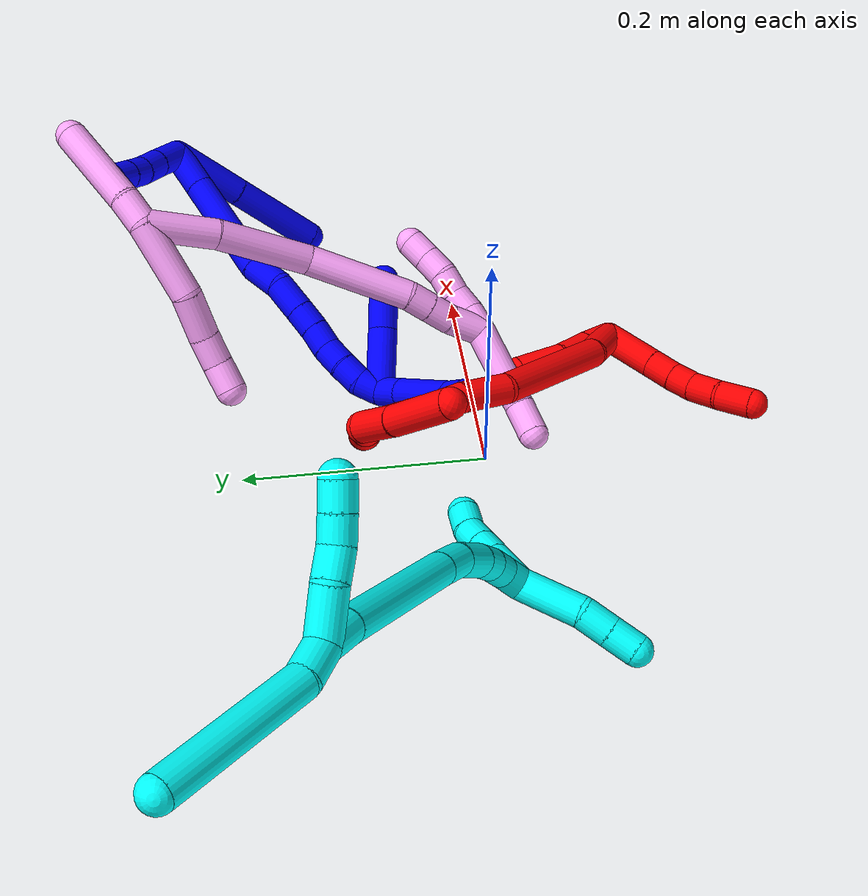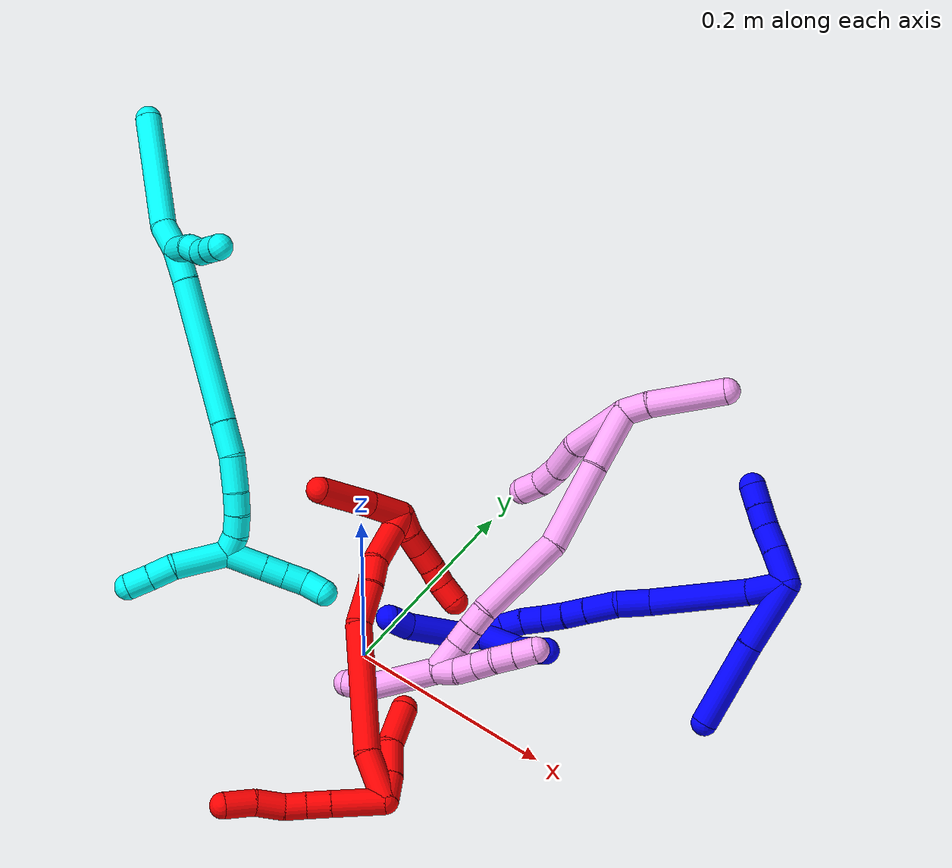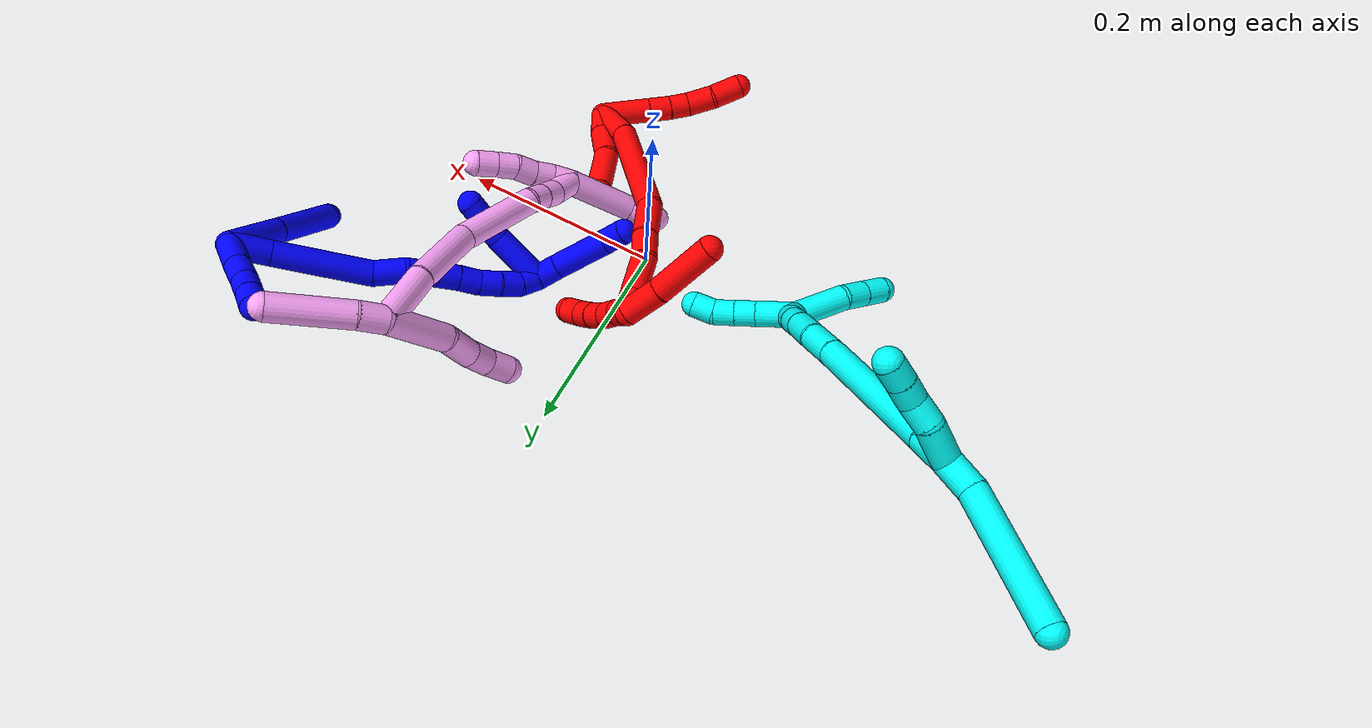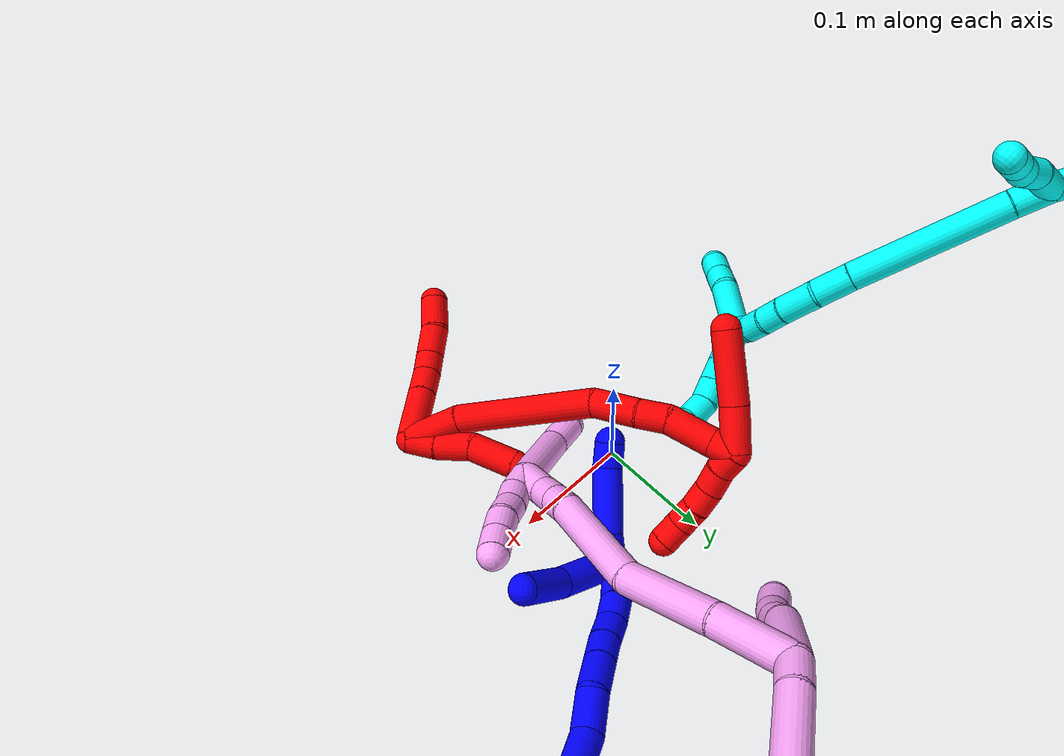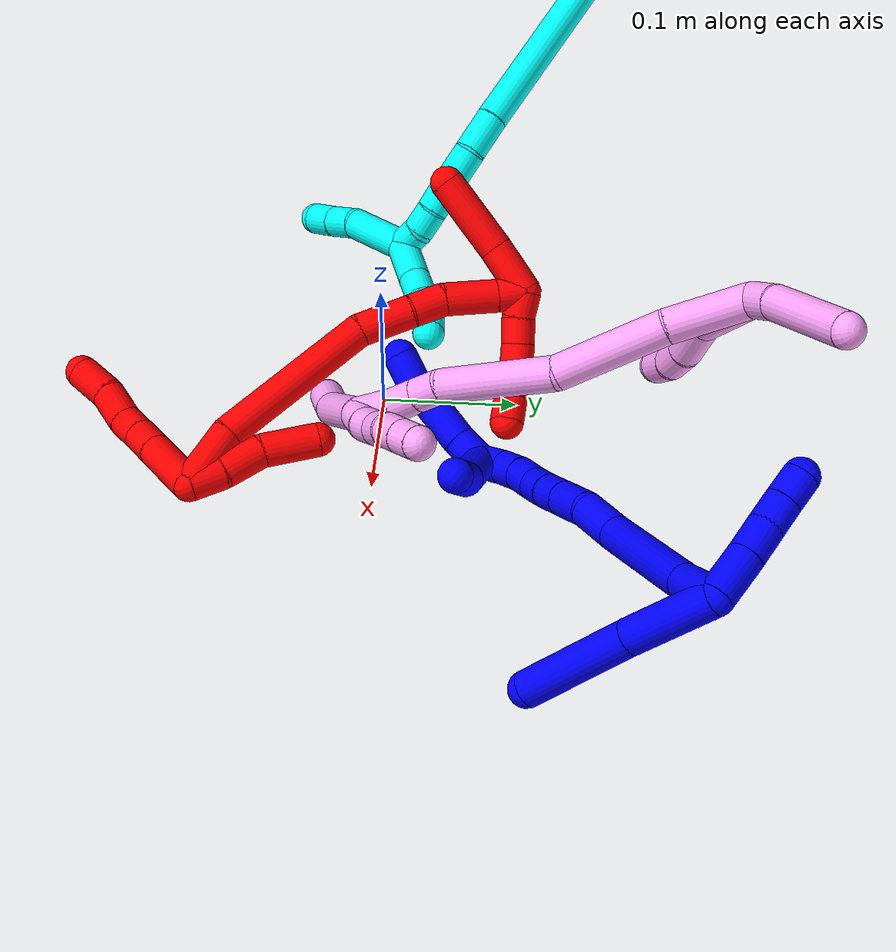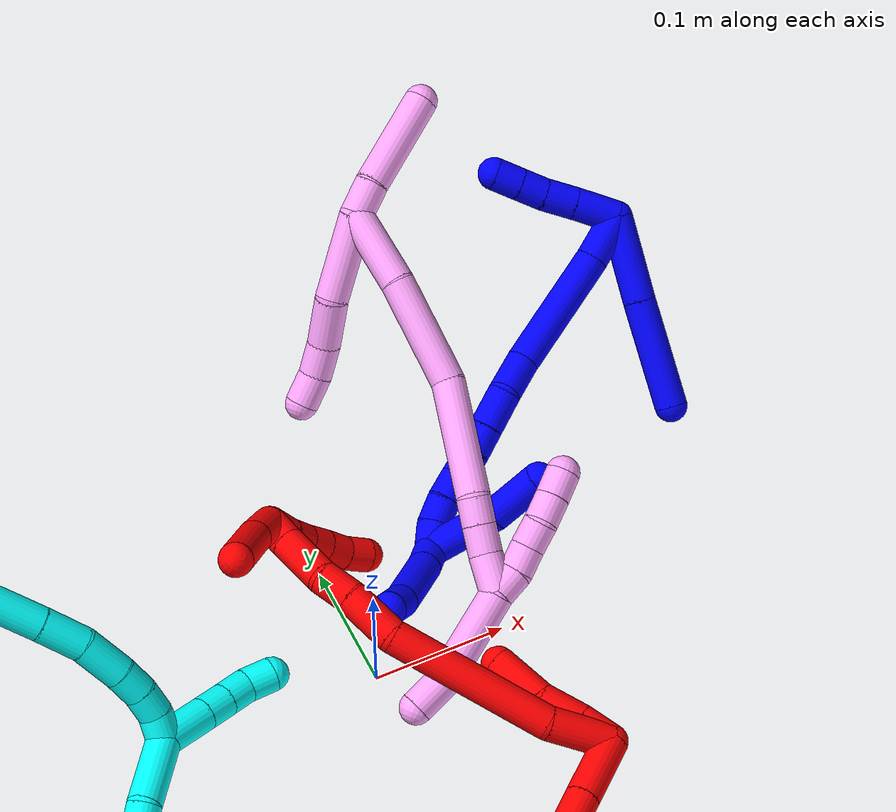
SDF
<sdf version="1.7">
 <world name="default">
  <plugin name="TubeGeneratorPlugin" filename="libtube_generator_plugin.so"/>
  <model name="photoneo_s_sensor">
   <static>1</static>
   <pose>0 0 2 1.57079 1.57079 3.14159</pose>
   <link name="link">
    <inertial><mass>0.1</mass></inertial>
    <sensor name="sensor" type="depth">
     <update_rate>30</update_rate>
     <camera>
      <horizontal_fov>1.22</horizontal_fov>
      <image><width>1920</width><height>1200</height><format>B8G8R8</format></image>
      <clip><near>0.1</near><far>4</far></clip>
      <depth_camera><output>points</output></depth_camera>
     </camera>
     <plugin name="camera_plugin" filename="libgazebo_ros_depth_camera.so">
      <baseline>0.2</baseline>
      <alwaysOn>1</alwaysOn>
      <updateRate>0.0</updateRate>
      <cameraName>camera_ir</cameraName>
      <imageTopicName>/camera/color/image_raw</imageTopicName>
      <cameraInfoTopicName>/camera/color/camera_info</cameraInfoTopicName>
      <depthImageTopicName>/camera/depth/image_raw</depthImageTopicName>
      <depthImageCameraInfoTopicName>/camera/depth/camera_info</depthImageCameraInfoTopicName>
      <pointCloudTopicName>/camera/depth/points</pointCloudTopicName>
      <frameName>fr_optical</frameName>
      <pointCloudCutoff>0.1</pointCloudCutoff>
      <pointCloudCutoffMax>2.0</pointCloudCutoffMax>
      <distortionK1>0</distortionK1>
      <distortionK2>0</distortionK2>
      <distortionK3>0</distortionK3>
      <distortionT1>0</distortionT1>
      <distortionT2>0</distortionT2>
      <CxPrime>0</CxPrime>
      <Cx>0</Cx>
      <Cy>0</Cy>
      <focalLength>0</focalLength>
      <hackBaseline>0</hackBaseline>
     </plugin>
    </sensor>
   </link>
  </model>
  <gravity>0 0 -9.8</gravity>
  <magnetic_field>6e-06 2.3e-05 -4.2e-05</magnetic_field>
  <atmosphere type="adiabatic"/>
  <physics name="default_physics" default="0" type="ode">
   <max_step_size>0.003</max_step_size>
   <real_time_factor>1</real_time_factor>
   <real_time_update_rate>1000</real_time_update_rate>
   <max_contacts>10000</max_contacts>
   <ode>
    <solver>
     <type>quick</type>
     <iters>100</iters>
     <sor>1.3</sor>
     <use_dynamic_moi_rescaling>0</use_dynamic_moi_rescaling>
    </solver>
    <constraints>
     <contact_max_correcting_vel>0</contact_max_correcting_vel>
     <contact_surface_layer>0.001</contact_surface_layer>
     <cfm>0</cfm>
     <erp>0.2</erp>
    </constraints>
   </ode>
  </physics>
  <scene><ambient>0.4 0.4 0.4 1</ambient><background>0.7 0.7 0.7 1</background><shadows>0</shadows></scene>
  <audio><device>default</device></audio>
  <spherical_coordinates>
   <surface_model>EARTH_WGS84</surface_model>
   <latitude_deg>0</latitude_deg>
   <longitude_deg>0</longitude_deg>
   <elevation>0</elevation>
   <heading_deg>0</heading_deg>
  </spherical_coordinates>
  <model name="bin">
   <static>1</static>
   <link name="bottom">
    <collision name="collision-bottom">
     <pose>0 0 -0.01 0 -0 0</pose>
     <geometry><box><size>0.8 0.6 0.02</size></box></geometry>
     <surface>
      <friction><ode><mu>100</mu><mu2>100</mu2></ode></friction>
      <contact><collide_bitmask>65535</collide_bitmask></contact>
     </surface>
    </collision>
   </link>
   <link name="west_wall">
    <collision name="collision-west_wall">
     <pose>-0.41 0 0.1 0 -0 0</pose>
     <geometry><box><size>0.02 0.6 0.2</size></box></geometry>
     <surface>
      <friction><ode><mu>100</mu><mu2>100</mu2></ode></friction>
      <contact><collide_bitmask>65535</collide_bitmask></contact>
     </surface>
    </collision>
   </link>
   <link name="east_wall">
    <collision name="collision-east_wall">
     <pose>0.41 0 0.1 0 -0 0</pose>
     <geometry><box><size>0.02 0.6 0.2</size></box></geometry>
     <surface>
      <friction><ode><mu>100</mu><mu2>100</mu2></ode></friction>
      <contact><collide_bitmask>65535</collide_bitmask></contact>
     </surface>
    </collision>
   </link>
   <link name="south_wall">
    <collision name="collision-south_wall">
     <pose>0 -0.31 0.1 0 -0 0</pose>
     <geometry><box><size>0.8 0.02 0.2</size></box></geometry>
     <surface>
      <friction><ode><mu>100</mu><mu2>100</mu2></ode></friction>
      <contact><collide_bitmask>65535</collide_bitmask></contact>
     </surface>
    </collision>
   </link>
   <link name="north_wall">
    <collision name="collision-north_wall">
     <pose>0 0.31 0.1 0 -0 0</pose>
     <geometry><box><size>0.8 0.02 0.2</size></box></geometry>
     <surface>
      <friction><ode><mu>100</mu><mu2>100</mu2></ode></friction>
      <contact><collide_bitmask>65535</collide_bitmask></contact>
     </surface>
    </collision>
   </link>
  </model>
  <model name="1">
   <static>0</static>
   <link name="1">
    <collision name="collision-cylinder-e_1_2_8">
     <pose>-0.008833 0.027546 -0.016125 -2.10041 -0.269965 0.465165</pose>
     <geometry><cylinder><radius>0.0125</radius><length>0.066236</length></cylinder></geometry>
     <surface>
      <friction><ode><mu>1.16</mu><mu2>1.16</mu2><slip1>0</slip1><slip2>0</slip2></ode></friction>
      <contact><ode><kp>1e+06</kp><kd>1</kd><max_vel>0</max_vel><min_depth>0.001</min_depth></ode></contact>
     </surface>
    </collision>
    <visual name="visual-cylinder-e_1_2_8">
     <pose>-0.008833 0.027546 -0.016125 -2.10041 -0.269965 0.465165</pose>
     <geometry><cylinder><radius>0.0125</radius><length>0.066236</length></cylinder></geometry>
     <material><ambient>0 0 1 1</ambient></material>
    </visual>
    <collision name="collision-cylinder-e_2_8_6">
     <pose>-0.028597 0.090712 -0.051375 -2.06353 -0.264087 0.437025</pose>
     <geometry><cylinder><radius>0.0125</radius><length>0.083764</length></cylinder></geometry>
     <surface>
      <friction><ode><mu>1.16</mu><mu2>1.16</mu2><slip1>0</slip1><slip2>0</slip2></ode></friction>
      <contact><ode><kp>1e+06</kp><kd>1</kd><max_vel>0</max_vel><min_depth>0.001</min_depth></ode></contact>
     </surface>
    </collision>
    <visual name="visual-cylinder-e_2_8_6">
     <pose>-0.028597 0.090712 -0.051375 -2.06353 -0.264087 0.437025</pose>
     <geometry><cylinder><radius>0.0125</radius><length>0.083764</length></cylinder></geometry>
     <material><ambient>0 0 1 1</ambient></material>
    </visual>
    <collision name="collision-cylinder-e_1_2_9">
     <pose>-0.007032 -0.015143 -0.003004 1.76665 -0.427419 -0.5168</pose>
     <geometry><cylinder><radius>0.0125</radius><length>0.033928</length></cylinder></geometry>
     <surface>
      <friction><ode><mu>1.16</mu><mu2>1.16</mu2><slip1>0</slip1><slip2>0</slip2></ode></friction>
      <contact><ode><kp>1e+06</kp><kd>1</kd><max_vel>0</max_vel><min_depth>0.001</min_depth></ode></contact>
     </surface>
    </collision>
    <visual name="visual-cylinder-e_1_2_9">
     <pose>-0.007032 -0.015143 -0.003004 1.76665 -0.427419 -0.5168</pose>
     <geometry><cylinder><radius>0.0125</radius><length>0.033928</length></cylinder></geometry>
     <material><ambient>0 0 1 1</ambient></material>
    </visual>
    <collision name="collision-cylinder-e_2_9_10">
     <pose>-0.019188 -0.041189 -0.008684 1.81145 -0.428139 -0.540825</pose>
     <geometry><cylinder><radius>0.0125</radius><length>0.024682</length></cylinder></geometry>
     <surface>
      <friction><ode><mu>1.16</mu><mu2>1.16</mu2><slip1>0</slip1><slip2>0</slip2></ode></friction>
      <contact><ode><kp>1e+06</kp><kd>1</kd><max_vel>0</max_vel><min_depth>0.001</min_depth></ode></contact>
     </surface>
    </collision>
    <visual name="visual-cylinder-e_2_9_10">
     <pose>-0.019188 -0.041189 -0.008684 1.81145 -0.428139 -0.540825</pose>
     <geometry><cylinder><radius>0.0125</radius><length>0.024682</length></cylinder></geometry>
     <material><ambient>0 0 1 1</ambient></material>
    </visual>
    <collision name="collision-cylinder-e_3_10_11">
     <pose>-0.027587 -0.06165 -0.013245 1.76551 -0.324405 -0.392989</pose>
     <geometry><cylinder><radius>0.0125</radius><length>0.020555</length></cylinder></geometry>
     <surface>
      <friction><ode><mu>1.16</mu><mu2>1.16</mu2><slip1>0</slip1><slip2>0</slip2></ode></friction>
      <contact><ode><kp>1e+06</kp><kd>1</kd><max_vel>0</max_vel><min_depth>0.001</min_depth></ode></contact>
     </surface>
    </collision>
    <visual name="visual-cylinder-e_3_10_11">
     <pose>-0.027587 -0.06165 -0.013245 1.76551 -0.324405 -0.392989</pose>
     <geometry><cylinder><radius>0.0125</radius><length>0.020555</length></cylinder></geometry>
     <material><ambient>0 0 1 1</ambient></material>
    </visual>
    <collision name="collision-cylinder-e_4_11_5">
     <pose>-0.034282 -0.080893 -0.01687 1.74857 -0.334395 -0.398249</pose>
     <geometry><cylinder><radius>0.0125</radius><length>0.020835</length></cylinder></geometry>
     <surface>
      <friction><ode><mu>1.16</mu><mu2>1.16</mu2><slip1>0</slip1><slip2>0</slip2></ode></friction>
      <contact><ode><kp>1e+06</kp><kd>1</kd><max_vel>0</max_vel><min_depth>0.001</min_depth></ode></contact>
     </surface>
    </collision>
    <visual name="visual-cylinder-e_4_11_5">
     <pose>-0.034282 -0.080893 -0.01687 1.74857 -0.334395 -0.398249</pose>
     <geometry><cylinder><radius>0.0125</radius><length>0.020835</length></cylinder></geometry>
     <material><ambient>0 0 1 1</ambient></material>
    </visual>
    <collision name="collision-cylinder-e_1_2_12">
     <pose>-0.011739 0.003357 -0.014537 -2.91464 -0.666651 2.50562</pose>
     <geometry><cylinder><radius>0.0125</radius><length>0.037967</length></cylinder></geometry>
     <surface>
      <friction><ode><mu>1.16</mu><mu2>1.16</mu2><slip1>0</slip1><slip2>0</slip2></ode></friction>
      <contact><ode><kp>1e+06</kp><kd>1</kd><max_vel>0</max_vel><min_depth>0.001</min_depth></ode></contact>
     </surface>
    </collision>
    <visual name="visual-cylinder-e_1_2_12">
     <pose>-0.011739 0.003357 -0.014537 -2.91464 -0.666651 2.50562</pose>
     <geometry><cylinder><radius>0.0125</radius><length>0.037967</length></cylinder></geometry>
     <material><ambient>0 0 1 1</ambient></material>
    </visual>
    <collision name="collision-cylinder-e_2_12_13">
     <pose>-0.051802 0.011009 -0.067551 -3.03043 -0.631612 2.80426</pose>
     <geometry><cylinder><radius>0.0125</radius><length>0.095943</length></cylinder></geometry>
     <surface>
      <friction><ode><mu>1.16</mu><mu2>1.16</mu2><slip1>0</slip1><slip2>0</slip2></ode></friction>
      <contact><ode><kp>1e+06</kp><kd>1</kd><max_vel>0</max_vel><min_depth>0.001</min_depth></ode></contact>
     </surface>
    </collision>
    <visual name="visual-cylinder-e_2_12_13">
     <pose>-0.051802 0.011009 -0.067551 -3.03043 -0.631612 2.80426</pose>
     <geometry><cylinder><radius>0.0125</radius><length>0.095943</length></cylinder></geometry>
     <material><ambient>0 0 1 1</ambient></material>
    </visual>
    <collision name="collision-cylinder-e_3_13_14">
     <pose>-0.084974 0.01592 -0.121149 -3.10087 -0.309965 2.88238</pose>
     <geometry><cylinder><radius>0.0125</radius><length>0.03178</length></cylinder></geometry>
     <surface>
      <friction><ode><mu>1.16</mu><mu2>1.16</mu2><slip1>0</slip1><slip2>0</slip2></ode></friction>
      <contact><ode><kp>1e+06</kp><kd>1</kd><max_vel>0</max_vel><min_depth>0.001</min_depth></ode></contact>
     </surface>
    </collision>
    <visual name="visual-cylinder-e_3_13_14">
     <pose>-0.084974 0.01592 -0.121149 -3.10087 -0.309965 2.88238</pose>
     <geometry><cylinder><radius>0.0125</radius><length>0.03178</length></cylinder></geometry>
     <material><ambient>0 0 1 1</ambient></material>
    </visual>
    <collision name="collision-cylinder-e_4_14_15">
     <pose>-0.098173 0.01934 -0.148506 -2.91633 -0.587065 2.42543</pose>
     <geometry><cylinder><radius>0.0125</radius><length>0.030156</length></cylinder></geometry>
     <surface>
      <friction><ode><mu>1.16</mu><mu2>1.16</mu2><slip1>0</slip1><slip2>0</slip2></ode></friction>
      <contact><ode><kp>1e+06</kp><kd>1</kd><max_vel>0</max_vel><min_depth>0.001</min_depth></ode></contact>
     </surface>
    </collision>
    <visual name="visual-cylinder-e_4_14_15">
     <pose>-0.098173 0.01934 -0.148506 -2.91633 -0.587065 2.42543</pose>
     <geometry><cylinder><radius>0.0125</radius><length>0.030156</length></cylinder></geometry>
     <material><ambient>0 0 1 1</ambient></material>
    </visual>
    <collision name="collision-cylinder-e_5_15_16">
     <pose>-0.11258 0.02423 -0.169338 -2.90358 -0.600293 2.40424</pose>
     <geometry><cylinder><radius>0.0125</radius><length>0.021439</length></cylinder></geometry>
     <surface>
      <friction><ode><mu>1.16</mu><mu2>1.16</mu2><slip1>0</slip1><slip2>0</slip2></ode></friction>
      <contact><ode><kp>1e+06</kp><kd>1</kd><max_vel>0</max_vel><min_depth>0.001</min_depth></ode></contact>
     </surface>
    </collision>
    <visual name="visual-cylinder-e_5_15_16">
     <pose>-0.11258 0.02423 -0.169338 -2.90358 -0.600293 2.40424</pose>
     <geometry><cylinder><radius>0.0125</radius><length>0.021439</length></cylinder></geometry>
     <material><ambient>0 0 1 1</ambient></material>
    </visual>
    <collision name="collision-cylinder-e_6_16_17">
     <pose>-0.125271 0.02779 -0.186114 -2.96315 -0.673805 2.64148</pose>
     <geometry><cylinder><radius>0.0125</radius><length>0.021271</length></cylinder></geometry>
     <surface>
      <friction><ode><mu>1.16</mu><mu2>1.16</mu2><slip1>0</slip1><slip2>0</slip2></ode></friction>
      <contact><ode><kp>1e+06</kp><kd>1</kd><max_vel>0</max_vel><min_depth>0.001</min_depth></ode></contact>
     </surface>
    </collision>
    <visual name="visual-cylinder-e_6_16_17">
     <pose>-0.125271 0.02779 -0.186114 -2.96315 -0.673805 2.64148</pose>
     <geometry><cylinder><radius>0.0125</radius><length>0.021271</length></cylinder></geometry>
     <material><ambient>0 0 1 1</ambient></material>
    </visual>
    <collision name="collision-cylinder-e_7_17_18">
     <pose>-0.13688 0.030383 -0.203477 -3.02056 -0.493161 2.66914</pose>
     <geometry><cylinder><radius>0.0125</radius><length>0.021008</length></cylinder></geometry>
     <surface>
      <friction><ode><mu>1.16</mu><mu2>1.16</mu2><slip1>0</slip1><slip2>0</slip2></ode></friction>
      <contact><ode><kp>1e+06</kp><kd>1</kd><max_vel>0</max_vel><min_depth>0.001</min_depth></ode></contact>
     </surface>
    </collision>
    <visual name="visual-cylinder-e_7_17_18">
     <pose>-0.13688 0.030383 -0.203477 -3.02056 -0.493161 2.66914</pose>
     <geometry><cylinder><radius>0.0125</radius><length>0.021008</length></cylinder></geometry>
     <material><ambient>0 0 1 1</ambient></material>
    </visual>
    <collision name="collision-cylinder-e_8_18_19">
     <pose>-0.146541 0.034071 -0.221366 -2.8543 -0.476844 2.06793</pose>
     <geometry><cylinder><radius>0.0125</radius><length>0.02043</length></cylinder></geometry>
     <surface>
      <friction><ode><mu>1.16</mu><mu2>1.16</mu2><slip1>0</slip1><slip2>0</slip2></ode></friction>
      <contact><ode><kp>1e+06</kp><kd>1</kd><max_vel>0</max_vel><min_depth>0.001</min_depth></ode></contact>
     </surface>
    </collision>
    <visual name="visual-cylinder-e_8_18_19">
     <pose>-0.146541 0.034071 -0.221366 -2.8543 -0.476844 2.06793</pose>
     <geometry><cylinder><radius>0.0125</radius><length>0.02043</length></cylinder></geometry>
     <material><ambient>0 0 1 1</ambient></material>
    </visual>
    <collision name="collision-cylinder-e_9_19_1">
     <pose>-0.152824 0.040521 -0.239151 -2.73802 -0.160073 0.747321</pose>
     <geometry><cylinder><radius>0.0125</radius><length>0.020005</length></cylinder></geometry>
     <surface>
      <friction><ode><mu>1.16</mu><mu2>1.16</mu2><slip1>0</slip1><slip2>0</slip2></ode></friction>
      <contact><ode><kp>1e+06</kp><kd>1</kd><max_vel>0</max_vel><min_depth>0.001</min_depth></ode></contact>
     </surface>
    </collision>
    <visual name="visual-cylinder-e_9_19_1">
     <pose>-0.152824 0.040521 -0.239151 -2.73802 -0.160073 0.747321</pose>
     <geometry><cylinder><radius>0.0125</radius><length>0.020005</length></cylinder></geometry>
     <material><ambient>0 0 1 1</ambient></material>
    </visual>
    <collision name="collision-cylinder-e_1_1_20">
     <pose>-0.152468 0.04357 -0.259515 3.0683 0.170718 2.33196</pose>
     <geometry><cylinder><radius>0.0125</radius><length>0.022961</length></cylinder></geometry>
     <surface>
      <friction><ode><mu>1.16</mu><mu2>1.16</mu2><slip1>0</slip1><slip2>0</slip2></ode></friction>
      <contact><ode><kp>1e+06</kp><kd>1</kd><max_vel>0</max_vel><min_depth>0.001</min_depth></ode></contact>
     </surface>
    </collision>
    <visual name="visual-cylinder-e_1_1_20">
     <pose>-0.152468 0.04357 -0.259515 3.0683 0.170718 2.33196</pose>
     <geometry><cylinder><radius>0.0125</radius><length>0.022961</length></cylinder></geometry>
     <material><ambient>0 0 1 1</ambient></material>
    </visual>
    <collision name="collision-cylinder-e_2_20_21">
     <pose>-0.145607 0.037311 -0.297466 2.94069 0.178509 1.4522</pose>
     <geometry><cylinder><radius>0.0125</radius><length>0.055308</length></cylinder></geometry>
     <surface>
      <friction><ode><mu>1.16</mu><mu2>1.16</mu2><slip1>0</slip1><slip2>0</slip2></ode></friction>
      <contact><ode><kp>1e+06</kp><kd>1</kd><max_vel>0</max_vel><min_depth>0.001</min_depth></ode></contact>
     </surface>
    </collision>
    <visual name="visual-cylinder-e_2_20_21">
     <pose>-0.145607 0.037311 -0.297466 2.94069 0.178509 1.4522</pose>
     <geometry><cylinder><radius>0.0125</radius><length>0.055308</length></cylinder></geometry>
     <material><ambient>0 0 1 1</ambient></material>
    </visual>
    <collision name="collision-cylinder-e_3_21_4">
     <pose>-0.137936 0.027649 -0.333752 2.72719 0.256956 1.10209</pose>
     <geometry><cylinder><radius>0.0125</radius><length>0.021731</length></cylinder></geometry>
     <surface>
      <friction><ode><mu>1.16</mu><mu2>1.16</mu2><slip1>0</slip1><slip2>0</slip2></ode></friction>
      <contact><ode><kp>1e+06</kp><kd>1</kd><max_vel>0</max_vel><min_depth>0.001</min_depth></ode></contact>
     </surface>
    </collision>
    <visual name="visual-cylinder-e_3_21_4">
     <pose>-0.137936 0.027649 -0.333752 2.72719 0.256956 1.10209</pose>
     <geometry><cylinder><radius>0.0125</radius><length>0.021731</length></cylinder></geometry>
     <material><ambient>0 0 1 1</ambient></material>
    </visual>
    <collision name="collision-cylinder-e_1_1_22">
     <pose>-0.12942 0.050502 -0.237286 -0.508647 1.1061 -0.318228</pose>
     <geometry><cylinder><radius>0.0125</radius><length>0.055927</length></cylinder></geometry>
     <surface>
      <friction><ode><mu>1.16</mu><mu2>1.16</mu2><slip1>0</slip1><slip2>0</slip2></ode></friction>
      <contact><ode><kp>1e+06</kp><kd>1</kd><max_vel>0</max_vel><min_depth>0.001</min_depth></ode></contact>
     </surface>
    </collision>
    <visual name="visual-cylinder-e_1_1_22">
     <pose>-0.12942 0.050502 -0.237286 -0.508647 1.1061 -0.318228</pose>
     <geometry><cylinder><radius>0.0125</radius><length>0.055927</length></cylinder></geometry>
     <material><ambient>0 0 1 1</ambient></material>
    </visual>
    <collision name="collision-cylinder-e_2_22_3">
     <pose>-0.083175 0.056143 -0.220513 0.079059 1.30226 0.060255</pose>
     <geometry><cylinder><radius>0.0125</radius><length>0.044073</length></cylinder></geometry>
     <surface>
      <friction><ode><mu>1.16</mu><mu2>1.16</mu2><slip1>0</slip1><slip2>0</slip2></ode></friction>
      <contact><ode><kp>1e+06</kp><kd>1</kd><max_vel>0</max_vel><min_depth>0.001</min_depth></ode></contact>
     </surface>
    </collision>
    <visual name="visual-cylinder-e_2_22_3">
     <pose>-0.083175 0.056143 -0.220513 0.079059 1.30226 0.060255</pose>
     <geometry><cylinder><radius>0.0125</radius><length>0.044073</length></cylinder></geometry>
     <material><ambient>0 0 1 1</ambient></material>
    </visual>
    <collision name="collision-sphere-3">
     <pose>-0.061929 0.055681 -0.214684 0 -0 0</pose>
     <geometry><sphere><radius>0.0125</radius></sphere></geometry>
     <surface>
      <friction><ode><mu>1.16</mu><mu2>1.16</mu2><slip1>0</slip1><slip2>0</slip2></ode></friction>
      <contact><ode><kp>1e+06</kp><kd>1</kd><max_vel>0</max_vel><min_depth>0.001</min_depth></ode></contact>
     </surface>
    </collision>
    <visual name="visual-sphere-3">
     <pose>-0.061929 0.055681 -0.214684 0 -0 0</pose>
     <geometry><sphere><radius>0.0125</radius></sphere></geometry>
     <material><ambient>0 0 1 1</ambient></material>
    </visual>
    <collision name="collision-sphere-22">
     <pose>-0.104422 0.056605 -0.226341 0 -0 0</pose>
     <geometry><sphere><radius>0.0125</radius></sphere></geometry>
     <surface>
      <friction><ode><mu>1.16</mu><mu2>1.16</mu2><slip1>0</slip1><slip2>0</slip2></ode></friction>
      <contact><ode><kp>1e+06</kp><kd>1</kd><max_vel>0</max_vel><min_depth>0.001</min_depth></ode></contact>
     </surface>
    </collision>
    <visual name="visual-sphere-22">
     <pose>-0.104422 0.056605 -0.226341 0 -0 0</pose>
     <geometry><sphere><radius>0.0125</radius></sphere></geometry>
     <material><ambient>0 0 1 1</ambient></material>
    </visual>
    <collision name="collision-sphere-4">
     <pose>-0.135174 0.023418 -0.343371 0 -0 0</pose>
     <geometry><sphere><radius>0.0125</radius></sphere></geometry>
     <surface>
      <friction><ode><mu>1.16</mu><mu2>1.16</mu2><slip1>0</slip1><slip2>0</slip2></ode></friction>
      <contact><ode><kp>1e+06</kp><kd>1</kd><max_vel>0</max_vel><min_depth>0.001</min_depth></ode></contact>
     </surface>
    </collision>
    <visual name="visual-sphere-4">
     <pose>-0.135174 0.023418 -0.343371 0 -0 0</pose>
     <geometry><sphere><radius>0.0125</radius></sphere></geometry>
     <material><ambient>0 0 1 1</ambient></material>
    </visual>
    <collision name="collision-sphere-21">
     <pose>-0.140697 0.03188 -0.324133 0 -0 0</pose>
     <geometry><sphere><radius>0.0125</radius></sphere></geometry>
     <surface>
      <friction><ode><mu>1.16</mu><mu2>1.16</mu2><slip1>0</slip1><slip2>0</slip2></ode></friction>
      <contact><ode><kp>1e+06</kp><kd>1</kd><max_vel>0</max_vel><min_depth>0.001</min_depth></ode></contact>
     </surface>
    </collision>
    <visual name="visual-sphere-21">
     <pose>-0.140697 0.03188 -0.324133 0 -0 0</pose>
     <geometry><sphere><radius>0.0125</radius></sphere></geometry>
     <material><ambient>0 0 1 1</ambient></material>
    </visual>
    <collision name="collision-sphere-20">
     <pose>-0.150518 0.042742 -0.270799 0 -0 0</pose>
     <geometry><sphere><radius>0.0125</radius></sphere></geometry>
     <surface>
      <friction><ode><mu>1.16</mu><mu2>1.16</mu2><slip1>0</slip1><slip2>0</slip2></ode></friction>
      <contact><ode><kp>1e+06</kp><kd>1</kd><max_vel>0</max_vel><min_depth>0.001</min_depth></ode></contact>
     </surface>
    </collision>
    <visual name="visual-sphere-20">
     <pose>-0.150518 0.042742 -0.270799 0 -0 0</pose>
     <geometry><sphere><radius>0.0125</radius></sphere></geometry>
     <material><ambient>0 0 1 1</ambient></material>
    </visual>
    <collision name="collision-sphere-11">
     <pose>-0.030863 -0.071207 -0.01513 0 -0 0</pose>
     <geometry><sphere><radius>0.0125</radius></sphere></geometry>
     <surface>
      <friction><ode><mu>1.16</mu><mu2>1.16</mu2><slip1>0</slip1><slip2>0</slip2></ode></friction>
      <contact><ode><kp>1e+06</kp><kd>1</kd><max_vel>0</max_vel><min_depth>0.001</min_depth></ode></contact>
     </surface>
    </collision>
    <visual name="visual-sphere-11">
     <pose>-0.030863 -0.071207 -0.01513 0 -0 0</pose>
     <geometry><sphere><radius>0.0125</radius></sphere></geometry>
     <material><ambient>0 0 1 1</ambient></material>
    </visual>
    <collision name="collision-sphere-10">
     <pose>-0.024311 -0.052093 -0.01136 0 -0 0</pose>
     <geometry><sphere><radius>0.0125</radius></sphere></geometry>
     <surface>
      <friction><ode><mu>1.16</mu><mu2>1.16</mu2><slip1>0</slip1><slip2>0</slip2></ode></friction>
      <contact><ode><kp>1e+06</kp><kd>1</kd><max_vel>0</max_vel><min_depth>0.001</min_depth></ode></contact>
     </surface>
    </collision>
    <visual name="visual-sphere-10">
     <pose>-0.024311 -0.052093 -0.01136 0 -0 0</pose>
     <geometry><sphere><radius>0.0125</radius></sphere></geometry>
     <material><ambient>0 0 1 1</ambient></material>
    </visual>
    <collision name="collision-sphere-6">
     <pose>-0.03953 0.126333 -0.0705 0 -0 0</pose>
     <geometry><sphere><radius>0.0125</radius></sphere></geometry>
     <surface>
      <friction><ode><mu>1.16</mu><mu2>1.16</mu2><slip1>0</slip1><slip2>0</slip2></ode></friction>
      <contact><ode><kp>1e+06</kp><kd>1</kd><max_vel>0</max_vel><min_depth>0.001</min_depth></ode></contact>
     </surface>
    </collision>
    <visual name="visual-sphere-6">
     <pose>-0.03953 0.126333 -0.0705 0 -0 0</pose>
     <geometry><sphere><radius>0.0125</radius></sphere></geometry>
     <material><ambient>0 0 1 1</ambient></material>
    </visual>
    <collision name="collision-sphere-9">
     <pose>-0.014064 -0.030285 -0.006008 0 -0 0</pose>
     <geometry><sphere><radius>0.0125</radius></sphere></geometry>
     <surface>
      <friction><ode><mu>1.16</mu><mu2>1.16</mu2><slip1>0</slip1><slip2>0</slip2></ode></friction>
      <contact><ode><kp>1e+06</kp><kd>1</kd><max_vel>0</max_vel><min_depth>0.001</min_depth></ode></contact>
     </surface>
    </collision>
    <visual name="visual-sphere-9">
     <pose>-0.014064 -0.030285 -0.006008 0 -0 0</pose>
     <geometry><sphere><radius>0.0125</radius></sphere></geometry>
     <material><ambient>0 0 1 1</ambient></material>
    </visual>
    <collision name="collision-sphere-2">
     <geometry><sphere><radius>0.0125</radius></sphere></geometry>
     <surface>
      <friction><ode><mu>1.16</mu><mu2>1.16</mu2><slip1>0</slip1><slip2>0</slip2></ode></friction>
      <contact><ode><kp>1e+06</kp><kd>1</kd><max_vel>0</max_vel><min_depth>0.001</min_depth></ode></contact>
     </surface>
    </collision>
    <visual name="visual-sphere-2">
     <geometry><sphere><radius>0.0125</radius></sphere></geometry>
     <material><ambient>0 0 1 1</ambient></material>
    </visual>
    <collision name="collision-sphere-19">
     <pose>-0.15123 0.036643 -0.230069 0 -0 0</pose>
     <geometry><sphere><radius>0.0125</radius></sphere></geometry>
     <surface>
      <friction><ode><mu>1.16</mu><mu2>1.16</mu2><slip1>0</slip1><slip2>0</slip2></ode></friction>
      <contact><ode><kp>1e+06</kp><kd>1</kd><max_vel>0</max_vel><min_depth>0.001</min_depth></ode></contact>
     </surface>
    </collision>
    <visual name="visual-sphere-19">
     <pose>-0.15123 0.036643 -0.230069 0 -0 0</pose>
     <geometry><sphere><radius>0.0125</radius></sphere></geometry>
     <material><ambient>0 0 1 1</ambient></material>
    </visual>
    <collision name="collision-sphere-8">
     <pose>-0.017665 0.055092 -0.032251 0 -0 0</pose>
     <geometry><sphere><radius>0.0125</radius></sphere></geometry>
     <surface>
      <friction><ode><mu>1.16</mu><mu2>1.16</mu2><slip1>0</slip1><slip2>0</slip2></ode></friction>
      <contact><ode><kp>1e+06</kp><kd>1</kd><max_vel>0</max_vel><min_depth>0.001</min_depth></ode></contact>
     </surface>
    </collision>
    <visual name="visual-sphere-8">
     <pose>-0.017665 0.055092 -0.032251 0 -0 0</pose>
     <geometry><sphere><radius>0.0125</radius></sphere></geometry>
     <material><ambient>0 0 1 1</ambient></material>
    </visual>
    <collision name="collision-sphere-5">
     <pose>-0.037701 -0.090578 -0.01861 0 -0 0</pose>
     <geometry><sphere><radius>0.0125</radius></sphere></geometry>
     <surface>
      <friction><ode><mu>1.16</mu><mu2>1.16</mu2><slip1>0</slip1><slip2>0</slip2></ode></friction>
      <contact><ode><kp>1e+06</kp><kd>1</kd><max_vel>0</max_vel><min_depth>0.001</min_depth></ode></contact>
     </surface>
    </collision>
    <visual name="visual-sphere-5">
     <pose>-0.037701 -0.090578 -0.01861 0 -0 0</pose>
     <geometry><sphere><radius>0.0125</radius></sphere></geometry>
     <material><ambient>0 0 1 1</ambient></material>
    </visual>
    <collision name="collision-sphere-12">
     <pose>-0.023477 0.006714 -0.029073 0 -0 0</pose>
     <geometry><sphere><radius>0.0125</radius></sphere></geometry>
     <surface>
      <friction><ode><mu>1.16</mu><mu2>1.16</mu2><slip1>0</slip1><slip2>0</slip2></ode></friction>
      <contact><ode><kp>1e+06</kp><kd>1</kd><max_vel>0</max_vel><min_depth>0.001</min_depth></ode></contact>
     </surface>
    </collision>
    <visual name="visual-sphere-12">
     <pose>-0.023477 0.006714 -0.029073 0 -0 0</pose>
     <geometry><sphere><radius>0.0125</radius></sphere></geometry>
     <material><ambient>0 0 1 1</ambient></material>
    </visual>
    <collision name="collision-sphere-13">
     <pose>-0.080127 0.015304 -0.106029 0 -0 0</pose>
     <geometry><sphere><radius>0.0125</radius></sphere></geometry>
     <surface>
      <friction><ode><mu>1.16</mu><mu2>1.16</mu2><slip1>0</slip1><slip2>0</slip2></ode></friction>
      <contact><ode><kp>1e+06</kp><kd>1</kd><max_vel>0</max_vel><min_depth>0.001</min_depth></ode></contact>
     </surface>
    </collision>
    <visual name="visual-sphere-13">
     <pose>-0.080127 0.015304 -0.106029 0 -0 0</pose>
     <geometry><sphere><radius>0.0125</radius></sphere></geometry>
     <material><ambient>0 0 1 1</ambient></material>
    </visual>
    <collision name="collision-sphere-14">
     <pose>-0.089821 0.016536 -0.13627 0 -0 0</pose>
     <geometry><sphere><radius>0.0125</radius></sphere></geometry>
     <surface>
      <friction><ode><mu>1.16</mu><mu2>1.16</mu2><slip1>0</slip1><slip2>0</slip2></ode></friction>
      <contact><ode><kp>1e+06</kp><kd>1</kd><max_vel>0</max_vel><min_depth>0.001</min_depth></ode></contact>
     </surface>
    </collision>
    <visual name="visual-sphere-14">
     <pose>-0.089821 0.016536 -0.13627 0 -0 0</pose>
     <geometry><sphere><radius>0.0125</radius></sphere></geometry>
     <material><ambient>0 0 1 1</ambient></material>
    </visual>
    <collision name="collision-sphere-15">
     <pose>-0.106524 0.022144 -0.160742 0 -0 0</pose>
     <geometry><sphere><radius>0.0125</radius></sphere></geometry>
     <surface>
      <friction><ode><mu>1.16</mu><mu2>1.16</mu2><slip1>0</slip1><slip2>0</slip2></ode></friction>
      <contact><ode><kp>1e+06</kp><kd>1</kd><max_vel>0</max_vel><min_depth>0.001</min_depth></ode></contact>
     </surface>
    </collision>
    <visual name="visual-sphere-15">
     <pose>-0.106524 0.022144 -0.160742 0 -0 0</pose>
     <geometry><sphere><radius>0.0125</radius></sphere></geometry>
     <material><ambient>0 0 1 1</ambient></material>
    </visual>
    <collision name="collision-sphere-16">
     <pose>-0.118635 0.026315 -0.177934 0 -0 0</pose>
     <geometry><sphere><radius>0.0125</radius></sphere></geometry>
     <surface>
      <friction><ode><mu>1.16</mu><mu2>1.16</mu2><slip1>0</slip1><slip2>0</slip2></ode></friction>
      <contact><ode><kp>1e+06</kp><kd>1</kd><max_vel>0</max_vel><min_depth>0.001</min_depth></ode></contact>
     </surface>
    </collision>
    <visual name="visual-sphere-16">
     <pose>-0.118635 0.026315 -0.177934 0 -0 0</pose>
     <geometry><sphere><radius>0.0125</radius></sphere></geometry>
     <material><ambient>0 0 1 1</ambient></material>
    </visual>
    <collision name="collision-sphere-17">
     <pose>-0.131907 0.029265 -0.194293 0 -0 0</pose>
     <geometry><sphere><radius>0.0125</radius></sphere></geometry>
     <surface>
      <friction><ode><mu>1.16</mu><mu2>1.16</mu2><slip1>0</slip1><slip2>0</slip2></ode></friction>
      <contact><ode><kp>1e+06</kp><kd>1</kd><max_vel>0</max_vel><min_depth>0.001</min_depth></ode></contact>
     </surface>
    </collision>
    <visual name="visual-sphere-17">
     <pose>-0.131907 0.029265 -0.194293 0 -0 0</pose>
     <geometry><sphere><radius>0.0125</radius></sphere></geometry>
     <material><ambient>0 0 1 1</ambient></material>
    </visual>
    <collision name="collision-sphere-18">
     <pose>-0.141853 0.0315 -0.212662 0 -0 0</pose>
     <geometry><sphere><radius>0.0125</radius></sphere></geometry>
     <surface>
      <friction><ode><mu>1.16</mu><mu2>1.16</mu2><slip1>0</slip1><slip2>0</slip2></ode></friction>
      <contact><ode><kp>1e+06</kp><kd>1</kd><max_vel>0</max_vel><min_depth>0.001</min_depth></ode></contact>
     </surface>
    </collision>
    <visual name="visual-sphere-18">
     <pose>-0.141853 0.0315 -0.212662 0 -0 0</pose>
     <geometry><sphere><radius>0.0125</radius></sphere></geometry>
     <material><ambient>0 0 1 1</ambient></material>
    </visual>
    <collision name="collision-sphere-1">
     <pose>-0.154418 0.044399 -0.248232 0 -0 0</pose>
     <geometry><sphere><radius>0.0125</radius></sphere></geometry>
     <surface>
      <friction><ode><mu>1.16</mu><mu2>1.16</mu2><slip1>0</slip1><slip2>0</slip2></ode></friction>
      <contact><ode><kp>1e+06</kp><kd>1</kd><max_vel>0</max_vel><min_depth>0.001</min_depth></ode></contact>
     </surface>
    </collision>
    <visual name="visual-sphere-1">
     <pose>-0.154418 0.044399 -0.248232 0 -0 0</pose>
     <geometry><sphere><radius>0.0125</radius></sphere></geometry>
     <material><ambient>0 0 1 1</ambient></material>
    </visual>
    <inertial>
     <pose>-0.074015 0.025909 -0.127329 0 -0 0</pose>
     <mass>0.75</mass>
     <inertia><ixx>8.3e-05</ixx><ixy>0</ixy><ixz>0</ixz><iyy>0.00017</iyy><iyz>0</iyz><izz>-4.5e-05</izz></inertia>
    </inertial>
   </link>
   <pose>0.311622 0.234849 0.108323 -1.85806 -0.842935 -0.517126</pose>
  </model>
  <model name="2">
   <static>0</static>
   <link name="2">
    <collision name="collision-cylinder-e_1_2_8">
     <pose>-0.023651 -0.005801 0.003019 1.09096 -1.30105 -0.865363</pose>
     <geometry><cylinder><radius>0.0125</radius><length>0.049076</length></cylinder></geometry>
     <surface>
      <friction><ode><mu>1.16</mu><mu2>1.16</mu2><slip1>0</slip1><slip2>0</slip2></ode></friction>
      <contact><ode><kp>1e+06</kp><kd>1</kd><max_vel>0</max_vel><min_depth>0.001</min_depth></ode></contact>
     </surface>
    </collision>
    <visual name="visual-cylinder-e_1_2_8">
     <pose>-0.023651 -0.005801 0.003019 1.09096 -1.30105 -0.865363</pose>
     <geometry><cylinder><radius>0.0125</radius><length>0.049076</length></cylinder></geometry>
     <material><ambient>1 0 0 1</ambient></material>
    </visual>
    <collision name="collision-cylinder-e_2_8_9">
     <pose>-0.058328 -0.014393 0.007398 1.11726 -1.29627 -0.884157</pose>
     <geometry><cylinder><radius>0.0125</radius><length>0.02291</length></cylinder></geometry>
     <surface>
      <friction><ode><mu>1.16</mu><mu2>1.16</mu2><slip1>0</slip1><slip2>0</slip2></ode></friction>
      <contact><ode><kp>1e+06</kp><kd>1</kd><max_vel>0</max_vel><min_depth>0.001</min_depth></ode></contact>
     </surface>
    </collision>
    <visual name="visual-cylinder-e_2_8_9">
     <pose>-0.058328 -0.014393 0.007398 1.11726 -1.29627 -0.884157</pose>
     <geometry><cylinder><radius>0.0125</radius><length>0.02291</length></cylinder></geometry>
     <material><ambient>1 0 0 1</ambient></material>
    </visual>
    <collision name="collision-cylinder-e_3_9_10">
     <pose>-0.079081 -0.0199 0.01066 0.960039 -1.24229 -0.713304</pose>
     <geometry><cylinder><radius>0.0125</radius><length>0.020554</length></cylinder></geometry>
     <surface>
      <friction><ode><mu>1.16</mu><mu2>1.16</mu2><slip1>0</slip1><slip2>0</slip2></ode></friction>
      <contact><ode><kp>1e+06</kp><kd>1</kd><max_vel>0</max_vel><min_depth>0.001</min_depth></ode></contact>
     </surface>
    </collision>
    <visual name="visual-cylinder-e_3_9_10">
     <pose>-0.079081 -0.0199 0.01066 0.960039 -1.24229 -0.713304</pose>
     <geometry><cylinder><radius>0.0125</radius><length>0.020554</length></cylinder></geometry>
     <material><ambient>1 0 0 1</ambient></material>
    </visual>
    <collision name="collision-cylinder-e_4_10_11">
     <pose>-0.10151 -0.023505 0.017973 0.162628 -1.16324 -0.107059</pose>
     <geometry><cylinder><radius>0.0125</radius><length>0.02767</length></cylinder></geometry>
     <surface>
      <friction><ode><mu>1.16</mu><mu2>1.16</mu2><slip1>0</slip1><slip2>0</slip2></ode></friction>
      <contact><ode><kp>1e+06</kp><kd>1</kd><max_vel>0</max_vel><min_depth>0.001</min_depth></ode></contact>
     </surface>
    </collision>
    <visual name="visual-cylinder-e_4_10_11">
     <pose>-0.10151 -0.023505 0.017973 0.162628 -1.16324 -0.107059</pose>
     <geometry><cylinder><radius>0.0125</radius><length>0.02767</length></cylinder></geometry>
     <material><ambient>1 0 0 1</ambient></material>
    </visual>
    <collision name="collision-cylinder-e_5_11_6">
     <pose>-0.127235 -0.028956 0.028991 0.683121 -1.06404 -0.412557</pose>
     <geometry><cylinder><radius>0.0125</radius><length>0.02979</length></cylinder></geometry>
     <surface>
      <friction><ode><mu>1.16</mu><mu2>1.16</mu2><slip1>0</slip1><slip2>0</slip2></ode></friction>
      <contact><ode><kp>1e+06</kp><kd>1</kd><max_vel>0</max_vel><min_depth>0.001</min_depth></ode></contact>
     </surface>
    </collision>
    <visual name="visual-cylinder-e_5_11_6">
     <pose>-0.127235 -0.028956 0.028991 0.683121 -1.06404 -0.412557</pose>
     <geometry><cylinder><radius>0.0125</radius><length>0.02979</length></cylinder></geometry>
     <material><ambient>1 0 0 1</ambient></material>
    </visual>
    <collision name="collision-cylinder-e_1_2_12">
     <pose>-0.000959 0.012029 -0.004758 -1.94743 -0.074038 0.108844</pose>
     <geometry><cylinder><radius>0.0125</radius><length>0.025942</length></cylinder></geometry>
     <surface>
      <friction><ode><mu>1.16</mu><mu2>1.16</mu2><slip1>0</slip1><slip2>0</slip2></ode></friction>
      <contact><ode><kp>1e+06</kp><kd>1</kd><max_vel>0</max_vel><min_depth>0.001</min_depth></ode></contact>
     </surface>
    </collision>
    <visual name="visual-cylinder-e_1_2_12">
     <pose>-0.000959 0.012029 -0.004758 -1.94743 -0.074038 0.108844</pose>
     <geometry><cylinder><radius>0.0125</radius><length>0.025942</length></cylinder></geometry>
     <material><ambient>1 0 0 1</ambient></material>
    </visual>
    <collision name="collision-cylinder-e_2_12_13">
     <pose>-0.005421 0.039109 -0.013981 -1.8592 -0.219467 0.293103</pose>
     <geometry><cylinder><radius>0.0125</radius><length>0.032171</length></cylinder></geometry>
     <surface>
      <friction><ode><mu>1.16</mu><mu2>1.16</mu2><slip1>0</slip1><slip2>0</slip2></ode></friction>
      <contact><ode><kp>1e+06</kp><kd>1</kd><max_vel>0</max_vel><min_depth>0.001</min_depth></ode></contact>
     </surface>
    </collision>
    <visual name="visual-cylinder-e_2_12_13">
     <pose>-0.005421 0.039109 -0.013981 -1.8592 -0.219467 0.293103</pose>
     <geometry><cylinder><radius>0.0125</radius><length>0.032171</length></cylinder></geometry>
     <material><ambient>1 0 0 1</ambient></material>
    </visual>
    <collision name="collision-cylinder-e_3_13_5">
     <pose>-0.007234 0.073005 -0.027426 -2.01546 0.080711 -0.127759</pose>
     <geometry><cylinder><radius>0.0125</radius><length>0.041887</length></cylinder></geometry>
     <surface>
      <friction><ode><mu>1.16</mu><mu2>1.16</mu2><slip1>0</slip1><slip2>0</slip2></ode></friction>
      <contact><ode><kp>1e+06</kp><kd>1</kd><max_vel>0</max_vel><min_depth>0.001</min_depth></ode></contact>
     </surface>
    </collision>
    <visual name="visual-cylinder-e_3_13_5">
     <pose>-0.007234 0.073005 -0.027426 -2.01546 0.080711 -0.127759</pose>
     <geometry><cylinder><radius>0.0125</radius><length>0.041887</length></cylinder></geometry>
     <material><ambient>1 0 0 1</ambient></material>
    </visual>
    <collision name="collision-cylinder-e_1_2_14">
     <pose>-0.012517 0.02037 -0.000249 -1.58304 -0.550991 0.557437</pose>
     <geometry><cylinder><radius>0.0125</radius><length>0.047819</length></cylinder></geometry>
     <surface>
      <friction><ode><mu>1.16</mu><mu2>1.16</mu2><slip1>0</slip1><slip2>0</slip2></ode></friction>
      <contact><ode><kp>1e+06</kp><kd>1</kd><max_vel>0</max_vel><min_depth>0.001</min_depth></ode></contact>
     </surface>
    </collision>
    <visual name="visual-cylinder-e_1_2_14">
     <pose>-0.012517 0.02037 -0.000249 -1.58304 -0.550991 0.557437</pose>
     <geometry><cylinder><radius>0.0125</radius><length>0.047819</length></cylinder></geometry>
     <material><ambient>1 0 0 1</ambient></material>
    </visual>
    <collision name="collision-cylinder-e_2_14_15">
     <pose>-0.041825 0.099947 -0.007994 -1.69671 -0.27424 0.310587</pose>
     <geometry><cylinder><radius>0.0125</radius><length>0.123994</length></cylinder></geometry>
     <surface>
      <friction><ode><mu>1.16</mu><mu2>1.16</mu2><slip1>0</slip1><slip2>0</slip2></ode></friction>
      <contact><ode><kp>1e+06</kp><kd>1</kd><max_vel>0</max_vel><min_depth>0.001</min_depth></ode></contact>
     </surface>
    </collision>
    <visual name="visual-cylinder-e_2_14_15">
     <pose>-0.041825 0.099947 -0.007994 -1.69671 -0.27424 0.310587</pose>
     <geometry><cylinder><radius>0.0125</radius><length>0.123994</length></cylinder></geometry>
     <material><ambient>1 0 0 1</ambient></material>
    </visual>
    <collision name="collision-cylinder-e_3_15_16">
     <pose>-0.057728 0.178868 -0.020838 -1.83576 0.043337 -0.056657</pose>
     <geometry><cylinder><radius>0.0125</radius><length>0.040892</length></cylinder></geometry>
     <surface>
      <friction><ode><mu>1.16</mu><mu2>1.16</mu2><slip1>0</slip1><slip2>0</slip2></ode></friction>
      <contact><ode><kp>1e+06</kp><kd>1</kd><max_vel>0</max_vel><min_depth>0.001</min_depth></ode></contact>
     </surface>
    </collision>
    <visual name="visual-cylinder-e_3_15_16">
     <pose>-0.057728 0.178868 -0.020838 -1.83576 0.043337 -0.056657</pose>
     <geometry><cylinder><radius>0.0125</radius><length>0.040892</length></cylinder></geometry>
     <material><ambient>1 0 0 1</ambient></material>
    </visual>
    <collision name="collision-cylinder-e_4_16_17">
     <pose>-0.057654 0.210805 -0.030677 -1.92281 -0.06225 0.089151</pose>
     <geometry><cylinder><radius>0.0125</radius><length>0.026093</length></cylinder></geometry>
     <surface>
      <friction><ode><mu>1.16</mu><mu2>1.16</mu2><slip1>0</slip1><slip2>0</slip2></ode></friction>
      <contact><ode><kp>1e+06</kp><kd>1</kd><max_vel>0</max_vel><min_depth>0.001</min_depth></ode></contact>
     </surface>
    </collision>
    <visual name="visual-cylinder-e_4_16_17">
     <pose>-0.057654 0.210805 -0.030677 -1.92281 -0.06225 0.089151</pose>
     <geometry><cylinder><radius>0.0125</radius><length>0.026093</length></cylinder></geometry>
     <material><ambient>1 0 0 1</ambient></material>
    </visual>
    <collision name="collision-cylinder-e_5_17_18">
     <pose>-0.055021 0.240211 -0.045041 -2.09234 0.172108 -0.295951</pose>
     <geometry><cylinder><radius>0.0125</radius><length>0.040231</length></cylinder></geometry>
     <surface>
      <friction><ode><mu>1.16</mu><mu2>1.16</mu2><slip1>0</slip1><slip2>0</slip2></ode></friction>
      <contact><ode><kp>1e+06</kp><kd>1</kd><max_vel>0</max_vel><min_depth>0.001</min_depth></ode></contact>
     </surface>
    </collision>
    <visual name="visual-cylinder-e_5_17_18">
     <pose>-0.055021 0.240211 -0.045041 -2.09234 0.172108 -0.295951</pose>
     <geometry><cylinder><radius>0.0125</radius><length>0.040231</length></cylinder></geometry>
     <material><ambient>1 0 0 1</ambient></material>
    </visual>
    <collision name="collision-cylinder-e_6_18_1">
     <pose>-0.049719 0.266807 -0.059146 -1.99327 0.178036 -0.274232</pose>
     <geometry><cylinder><radius>0.0125</radius><length>0.020971</length></cylinder></geometry>
     <surface>
      <friction><ode><mu>1.16</mu><mu2>1.16</mu2><slip1>0</slip1><slip2>0</slip2></ode></friction>
      <contact><ode><kp>1e+06</kp><kd>1</kd><max_vel>0</max_vel><min_depth>0.001</min_depth></ode></contact>
     </surface>
    </collision>
    <visual name="visual-cylinder-e_6_18_1">
     <pose>-0.049719 0.266807 -0.059146 -1.99327 0.178036 -0.274232</pose>
     <geometry><cylinder><radius>0.0125</radius><length>0.020971</length></cylinder></geometry>
     <material><ambient>1 0 0 1</ambient></material>
    </visual>
    <collision name="collision-cylinder-e_1_1_19">
     <pose>-0.043569 0.268875 -0.068634 2.19205 0.443674 0.827042</pose>
     <geometry><cylinder><radius>0.0125</radius><length>0.02</length></cylinder></geometry>
     <surface>
      <friction><ode><mu>1.16</mu><mu2>1.16</mu2><slip1>0</slip1><slip2>0</slip2></ode></friction>
      <contact><ode><kp>1e+06</kp><kd>1</kd><max_vel>0</max_vel><min_depth>0.001</min_depth></ode></contact>
     </surface>
    </collision>
    <visual name="visual-cylinder-e_1_1_19">
     <pose>-0.043569 0.268875 -0.068634 2.19205 0.443674 0.827042</pose>
     <geometry><cylinder><radius>0.0125</radius><length>0.02</length></cylinder></geometry>
     <material><ambient>1 0 0 1</ambient></material>
    </visual>
    <collision name="collision-cylinder-e_2_19_20">
     <pose>-0.03389 0.255917 -0.080173 2.41221 0.568838 1.30703</pose>
     <geometry><cylinder><radius>0.0125</radius><length>0.02</length></cylinder></geometry>
     <surface>
      <friction><ode><mu>1.16</mu><mu2>1.16</mu2><slip1>0</slip1><slip2>0</slip2></ode></friction>
      <contact><ode><kp>1e+06</kp><kd>1</kd><max_vel>0</max_vel><min_depth>0.001</min_depth></ode></contact>
     </surface>
    </collision>
    <visual name="visual-cylinder-e_2_19_20">
     <pose>-0.03389 0.255917 -0.080173 2.41221 0.568838 1.30703</pose>
     <geometry><cylinder><radius>0.0125</radius><length>0.02</length></cylinder></geometry>
     <material><ambient>1 0 0 1</ambient></material>
    </visual>
    <collision name="collision-cylinder-e_3_20_21">
     <pose>-0.022441 0.24414 -0.091482 2.25515 0.651432 1.23676</pose>
     <geometry><cylinder><radius>0.0125</radius><length>0.02</length></cylinder></geometry>
     <surface>
      <friction><ode><mu>1.16</mu><mu2>1.16</mu2><slip1>0</slip1><slip2>0</slip2></ode></friction>
      <contact><ode><kp>1e+06</kp><kd>1</kd><max_vel>0</max_vel><min_depth>0.001</min_depth></ode></contact>
     </surface>
    </collision>
    <visual name="visual-cylinder-e_3_20_21">
     <pose>-0.022441 0.24414 -0.091482 2.25515 0.651432 1.23676</pose>
     <geometry><cylinder><radius>0.0125</radius><length>0.02</length></cylinder></geometry>
     <material><ambient>1 0 0 1</ambient></material>
    </visual>
    <collision name="collision-cylinder-e_4_21_22">
     <pose>-0.010662 0.231043 -0.100895 2.13463 0.608369 1.03601</pose>
     <geometry><cylinder><radius>0.0125</radius><length>0.02</length></cylinder></geometry>
     <surface>
      <friction><ode><mu>1.16</mu><mu2>1.16</mu2><slip1>0</slip1><slip2>0</slip2></ode></friction>
      <contact><ode><kp>1e+06</kp><kd>1</kd><max_vel>0</max_vel><min_depth>0.001</min_depth></ode></contact>
     </surface>
    </collision>
    <visual name="visual-cylinder-e_4_21_22">
     <pose>-0.010662 0.231043 -0.100895 2.13463 0.608369 1.03601</pose>
     <geometry><cylinder><radius>0.0125</radius><length>0.02</length></cylinder></geometry>
     <material><ambient>1 0 0 1</ambient></material>
    </visual>
    <collision name="collision-cylinder-e_5_22_4">
     <pose>0.002185 0.217758 -0.10825 2.00832 0.793998 1.16531</pose>
     <geometry><cylinder><radius>0.0125</radius><length>0.02</length></cylinder></geometry>
     <surface>
      <friction><ode><mu>1.16</mu><mu2>1.16</mu2><slip1>0</slip1><slip2>0</slip2></ode></friction>
      <contact><ode><kp>1e+06</kp><kd>1</kd><max_vel>0</max_vel><min_depth>0.001</min_depth></ode></contact>
     </surface>
    </collision>
    <visual name="visual-cylinder-e_5_22_4">
     <pose>0.002185 0.217758 -0.10825 2.00832 0.793998 1.16531</pose>
     <geometry><cylinder><radius>0.0125</radius><length>0.02</length></cylinder></geometry>
     <material><ambient>1 0 0 1</ambient></material>
    </visual>
    <collision name="collision-cylinder-e_1_1_23">
     <pose>-0.061426 0.276203 -0.04957 0.001203 -0.77651 -0.000492</pose>
     <geometry><cylinder><radius>0.0125</radius><length>0.038709</length></cylinder></geometry>
     <surface>
      <friction><ode><mu>1.16</mu><mu2>1.16</mu2><slip1>0</slip1><slip2>0</slip2></ode></friction>
      <contact><ode><kp>1e+06</kp><kd>1</kd><max_vel>0</max_vel><min_depth>0.001</min_depth></ode></contact>
     </surface>
    </collision>
    <visual name="visual-cylinder-e_1_1_23">
     <pose>-0.061426 0.276203 -0.04957 0.001203 -0.77651 -0.000492</pose>
     <geometry><cylinder><radius>0.0125</radius><length>0.038709</length></cylinder></geometry>
     <material><ambient>1 0 0 1</ambient></material>
    </visual>
    <collision name="collision-cylinder-e_2_23_3">
     <pose>-0.094664 0.274656 -0.012318 0.065202 -0.697138 -0.023702</pose>
     <geometry><cylinder><radius>0.0125</radius><length>0.061291</length></cylinder></geometry>
     <surface>
      <friction><ode><mu>1.16</mu><mu2>1.16</mu2><slip1>0</slip1><slip2>0</slip2></ode></friction>
      <contact><ode><kp>1e+06</kp><kd>1</kd><max_vel>0</max_vel><min_depth>0.001</min_depth></ode></contact>
     </surface>
    </collision>
    <visual name="visual-cylinder-e_2_23_3">
     <pose>-0.094664 0.274656 -0.012318 0.065202 -0.697138 -0.023702</pose>
     <geometry><cylinder><radius>0.0125</radius><length>0.061291</length></cylinder></geometry>
     <material><ambient>1 0 0 1</ambient></material>
    </visual>
    <collision name="collision-sphere-3">
     <pose>-0.11434 0.273125 0.011127 0 -0 0</pose>
     <geometry><sphere><radius>0.0125</radius></sphere></geometry>
     <surface>
      <friction><ode><mu>1.16</mu><mu2>1.16</mu2><slip1>0</slip1><slip2>0</slip2></ode></friction>
      <contact><ode><kp>1e+06</kp><kd>1</kd><max_vel>0</max_vel><min_depth>0.001</min_depth></ode></contact>
     </surface>
    </collision>
    <visual name="visual-sphere-3">
     <pose>-0.11434 0.273125 0.011127 0 -0 0</pose>
     <geometry><sphere><radius>0.0125</radius></sphere></geometry>
     <material><ambient>1 0 0 1</ambient></material>
    </visual>
    <collision name="collision-sphere-23">
     <pose>-0.074989 0.276186 -0.035763 0 -0 0</pose>
     <geometry><sphere><radius>0.0125</radius></sphere></geometry>
     <surface>
      <friction><ode><mu>1.16</mu><mu2>1.16</mu2><slip1>0</slip1><slip2>0</slip2></ode></friction>
      <contact><ode><kp>1e+06</kp><kd>1</kd><max_vel>0</max_vel><min_depth>0.001</min_depth></ode></contact>
     </surface>
    </collision>
    <visual name="visual-sphere-23">
     <pose>-0.074989 0.276186 -0.035763 0 -0 0</pose>
     <geometry><sphere><radius>0.0125</radius></sphere></geometry>
     <material><ambient>1 0 0 1</ambient></material>
    </visual>
    <collision name="collision-sphere-4">
     <pose>0.009317 0.211408 -0.11122 0 -0 0</pose>
     <geometry><sphere><radius>0.0125</radius></sphere></geometry>
     <surface>
      <friction><ode><mu>1.16</mu><mu2>1.16</mu2><slip1>0</slip1><slip2>0</slip2></ode></friction>
      <contact><ode><kp>1e+06</kp><kd>1</kd><max_vel>0</max_vel><min_depth>0.001</min_depth></ode></contact>
     </surface>
    </collision>
    <visual name="visual-sphere-4">
     <pose>0.009317 0.211408 -0.11122 0 -0 0</pose>
     <geometry><sphere><radius>0.0125</radius></sphere></geometry>
     <material><ambient>1 0 0 1</ambient></material>
    </visual>
    <collision name="collision-sphere-22">
     <pose>-0.004947 0.224107 -0.10528 0 -0 0</pose>
     <geometry><sphere><radius>0.0125</radius></sphere></geometry>
     <surface>
      <friction><ode><mu>1.16</mu><mu2>1.16</mu2><slip1>0</slip1><slip2>0</slip2></ode></friction>
      <contact><ode><kp>1e+06</kp><kd>1</kd><max_vel>0</max_vel><min_depth>0.001</min_depth></ode></contact>
     </surface>
    </collision>
    <visual name="visual-sphere-22">
     <pose>-0.004947 0.224107 -0.10528 0 -0 0</pose>
     <geometry><sphere><radius>0.0125</radius></sphere></geometry>
     <material><ambient>1 0 0 1</ambient></material>
    </visual>
    <collision name="collision-sphere-21">
     <pose>-0.016377 0.237979 -0.096509 0 -0 0</pose>
     <geometry><sphere><radius>0.0125</radius></sphere></geometry>
     <surface>
      <friction><ode><mu>1.16</mu><mu2>1.16</mu2><slip1>0</slip1><slip2>0</slip2></ode></friction>
      <contact><ode><kp>1e+06</kp><kd>1</kd><max_vel>0</max_vel><min_depth>0.001</min_depth></ode></contact>
     </surface>
    </collision>
    <visual name="visual-sphere-21">
     <pose>-0.016377 0.237979 -0.096509 0 -0 0</pose>
     <geometry><sphere><radius>0.0125</radius></sphere></geometry>
     <material><ambient>1 0 0 1</ambient></material>
    </visual>
    <collision name="collision-sphere-20">
     <pose>-0.028504 0.250302 -0.086455 0 -0 0</pose>
     <geometry><sphere><radius>0.0125</radius></sphere></geometry>
     <surface>
      <friction><ode><mu>1.16</mu><mu2>1.16</mu2><slip1>0</slip1><slip2>0</slip2></ode></friction>
      <contact><ode><kp>1e+06</kp><kd>1</kd><max_vel>0</max_vel><min_depth>0.001</min_depth></ode></contact>
     </surface>
    </collision>
    <visual name="visual-sphere-20">
     <pose>-0.028504 0.250302 -0.086455 0 -0 0</pose>
     <geometry><sphere><radius>0.0125</radius></sphere></geometry>
     <material><ambient>1 0 0 1</ambient></material>
    </visual>
    <collision name="collision-sphere-6">
     <pose>-0.140258 -0.033519 0.034598 0 -0 0</pose>
     <geometry><sphere><radius>0.0125</radius></sphere></geometry>
     <surface>
      <friction><ode><mu>1.16</mu><mu2>1.16</mu2><slip1>0</slip1><slip2>0</slip2></ode></friction>
      <contact><ode><kp>1e+06</kp><kd>1</kd><max_vel>0</max_vel><min_depth>0.001</min_depth></ode></contact>
     </surface>
    </collision>
    <visual name="visual-sphere-6">
     <pose>-0.140258 -0.033519 0.034598 0 -0 0</pose>
     <geometry><sphere><radius>0.0125</radius></sphere></geometry>
     <material><ambient>1 0 0 1</ambient></material>
    </visual>
    <collision name="collision-sphere-11">
     <pose>-0.114212 -0.024393 0.023384 0 -0 0</pose>
     <geometry><sphere><radius>0.0125</radius></sphere></geometry>
     <surface>
      <friction><ode><mu>1.16</mu><mu2>1.16</mu2><slip1>0</slip1><slip2>0</slip2></ode></friction>
      <contact><ode><kp>1e+06</kp><kd>1</kd><max_vel>0</max_vel><min_depth>0.001</min_depth></ode></contact>
     </surface>
    </collision>
    <visual name="visual-sphere-11">
     <pose>-0.114212 -0.024393 0.023384 0 -0 0</pose>
     <geometry><sphere><radius>0.0125</radius></sphere></geometry>
     <material><ambient>1 0 0 1</ambient></material>
    </visual>
    <collision name="collision-sphere-10">
     <pose>-0.088809 -0.022617 0.012562 0 -0 0</pose>
     <geometry><sphere><radius>0.0125</radius></sphere></geometry>
     <surface>
      <friction><ode><mu>1.16</mu><mu2>1.16</mu2><slip1>0</slip1><slip2>0</slip2></ode></friction>
      <contact><ode><kp>1e+06</kp><kd>1</kd><max_vel>0</max_vel><min_depth>0.001</min_depth></ode></contact>
     </surface>
    </collision>
    <visual name="visual-sphere-10">
     <pose>-0.088809 -0.022617 0.012562 0 -0 0</pose>
     <geometry><sphere><radius>0.0125</radius></sphere></geometry>
     <material><ambient>1 0 0 1</ambient></material>
    </visual>
    <collision name="collision-sphere-9">
     <pose>-0.069354 -0.017184 0.008759 0 -0 0</pose>
     <geometry><sphere><radius>0.0125</radius></sphere></geometry>
     <surface>
      <friction><ode><mu>1.16</mu><mu2>1.16</mu2><slip1>0</slip1><slip2>0</slip2></ode></friction>
      <contact><ode><kp>1e+06</kp><kd>1</kd><max_vel>0</max_vel><min_depth>0.001</min_depth></ode></contact>
     </surface>
    </collision>
    <visual name="visual-sphere-9">
     <pose>-0.069354 -0.017184 0.008759 0 -0 0</pose>
     <geometry><sphere><radius>0.0125</radius></sphere></geometry>
     <material><ambient>1 0 0 1</ambient></material>
    </visual>
    <collision name="collision-sphere-2">
     <geometry><sphere><radius>0.0125</radius></sphere></geometry>
     <surface>
      <friction><ode><mu>1.16</mu><mu2>1.16</mu2><slip1>0</slip1><slip2>0</slip2></ode></friction>
      <contact><ode><kp>1e+06</kp><kd>1</kd><max_vel>0</max_vel><min_depth>0.001</min_depth></ode></contact>
     </surface>
    </collision>
    <visual name="visual-sphere-2">
     <geometry><sphere><radius>0.0125</radius></sphere></geometry>
     <material><ambient>1 0 0 1</ambient></material>
    </visual>
    <collision name="collision-sphere-19">
     <pose>-0.039277 0.261531 -0.073891 0 -0 0</pose>
     <geometry><sphere><radius>0.0125</radius></sphere></geometry>
     <surface>
      <friction><ode><mu>1.16</mu><mu2>1.16</mu2><slip1>0</slip1><slip2>0</slip2></ode></friction>
      <contact><ode><kp>1e+06</kp><kd>1</kd><max_vel>0</max_vel><min_depth>0.001</min_depth></ode></contact>
     </surface>
    </collision>
    <visual name="visual-sphere-19">
     <pose>-0.039277 0.261531 -0.073891 0 -0 0</pose>
     <geometry><sphere><radius>0.0125</radius></sphere></geometry>
     <material><ambient>1 0 0 1</ambient></material>
    </visual>
    <collision name="collision-sphere-8">
     <pose>-0.047302 -0.011601 0.006037 0 -0 0</pose>
     <geometry><sphere><radius>0.0125</radius></sphere></geometry>
     <surface>
      <friction><ode><mu>1.16</mu><mu2>1.16</mu2><slip1>0</slip1><slip2>0</slip2></ode></friction>
      <contact><ode><kp>1e+06</kp><kd>1</kd><max_vel>0</max_vel><min_depth>0.001</min_depth></ode></contact>
     </surface>
    </collision>
    <visual name="visual-sphere-8">
     <pose>-0.047302 -0.011601 0.006037 0 -0 0</pose>
     <geometry><sphere><radius>0.0125</radius></sphere></geometry>
     <material><ambient>1 0 0 1</ambient></material>
    </visual>
    <collision name="collision-sphere-12">
     <pose>-0.001919 0.024057 -0.009515 0 -0 0</pose>
     <geometry><sphere><radius>0.0125</radius></sphere></geometry>
     <surface>
      <friction><ode><mu>1.16</mu><mu2>1.16</mu2><slip1>0</slip1><slip2>0</slip2></ode></friction>
      <contact><ode><kp>1e+06</kp><kd>1</kd><max_vel>0</max_vel><min_depth>0.001</min_depth></ode></contact>
     </surface>
    </collision>
    <visual name="visual-sphere-12">
     <pose>-0.001919 0.024057 -0.009515 0 -0 0</pose>
     <geometry><sphere><radius>0.0125</radius></sphere></geometry>
     <material><ambient>1 0 0 1</ambient></material>
    </visual>
    <collision name="collision-sphere-13">
     <pose>-0.008923 0.05416 -0.018446 0 -0 0</pose>
     <geometry><sphere><radius>0.0125</radius></sphere></geometry>
     <surface>
      <friction><ode><mu>1.16</mu><mu2>1.16</mu2><slip1>0</slip1><slip2>0</slip2></ode></friction>
      <contact><ode><kp>1e+06</kp><kd>1</kd><max_vel>0</max_vel><min_depth>0.001</min_depth></ode></contact>
     </surface>
    </collision>
    <visual name="visual-sphere-13">
     <pose>-0.008923 0.05416 -0.018446 0 -0 0</pose>
     <geometry><sphere><radius>0.0125</radius></sphere></geometry>
     <material><ambient>1 0 0 1</ambient></material>
    </visual>
    <collision name="collision-sphere-5">
     <pose>-0.005546 0.091851 -0.036405 0 -0 0</pose>
     <geometry><sphere><radius>0.0125</radius></sphere></geometry>
     <surface>
      <friction><ode><mu>1.16</mu><mu2>1.16</mu2><slip1>0</slip1><slip2>0</slip2></ode></friction>
      <contact><ode><kp>1e+06</kp><kd>1</kd><max_vel>0</max_vel><min_depth>0.001</min_depth></ode></contact>
     </surface>
    </collision>
    <visual name="visual-sphere-5">
     <pose>-0.005546 0.091851 -0.036405 0 -0 0</pose>
     <geometry><sphere><radius>0.0125</radius></sphere></geometry>
     <material><ambient>1 0 0 1</ambient></material>
    </visual>
    <collision name="collision-sphere-14">
     <pose>-0.025035 0.040739 -0.000499 0 -0 0</pose>
     <geometry><sphere><radius>0.0125</radius></sphere></geometry>
     <surface>
      <friction><ode><mu>1.16</mu><mu2>1.16</mu2><slip1>0</slip1><slip2>0</slip2></ode></friction>
      <contact><ode><kp>1e+06</kp><kd>1</kd><max_vel>0</max_vel><min_depth>0.001</min_depth></ode></contact>
     </surface>
    </collision>
    <visual name="visual-sphere-14">
     <pose>-0.025035 0.040739 -0.000499 0 -0 0</pose>
     <geometry><sphere><radius>0.0125</radius></sphere></geometry>
     <material><ambient>1 0 0 1</ambient></material>
    </visual>
    <collision name="collision-sphere-15">
     <pose>-0.058614 0.159155 -0.015489 0 -0 0</pose>
     <geometry><sphere><radius>0.0125</radius></sphere></geometry>
     <surface>
      <friction><ode><mu>1.16</mu><mu2>1.16</mu2><slip1>0</slip1><slip2>0</slip2></ode></friction>
      <contact><ode><kp>1e+06</kp><kd>1</kd><max_vel>0</max_vel><min_depth>0.001</min_depth></ode></contact>
     </surface>
    </collision>
    <visual name="visual-sphere-15">
     <pose>-0.058614 0.159155 -0.015489 0 -0 0</pose>
     <geometry><sphere><radius>0.0125</radius></sphere></geometry>
     <material><ambient>1 0 0 1</ambient></material>
    </visual>
    <collision name="collision-sphere-16">
     <pose>-0.056843 0.198582 -0.026188 0 -0 0</pose>
     <geometry><sphere><radius>0.0125</radius></sphere></geometry>
     <surface>
      <friction><ode><mu>1.16</mu><mu2>1.16</mu2><slip1>0</slip1><slip2>0</slip2></ode></friction>
      <contact><ode><kp>1e+06</kp><kd>1</kd><max_vel>0</max_vel><min_depth>0.001</min_depth></ode></contact>
     </surface>
    </collision>
    <visual name="visual-sphere-16">
     <pose>-0.056843 0.198582 -0.026188 0 -0 0</pose>
     <geometry><sphere><radius>0.0125</radius></sphere></geometry>
     <material><ambient>1 0 0 1</ambient></material>
    </visual>
    <collision name="collision-sphere-17">
     <pose>-0.058466 0.223028 -0.035167 0 -0 0</pose>
     <geometry><sphere><radius>0.0125</radius></sphere></geometry>
     <surface>
      <friction><ode><mu>1.16</mu><mu2>1.16</mu2><slip1>0</slip1><slip2>0</slip2></ode></friction>
      <contact><ode><kp>1e+06</kp><kd>1</kd><max_vel>0</max_vel><min_depth>0.001</min_depth></ode></contact>
     </surface>
    </collision>
    <visual name="visual-sphere-17">
     <pose>-0.058466 0.223028 -0.035167 0 -0 0</pose>
     <geometry><sphere><radius>0.0125</radius></sphere></geometry>
     <material><ambient>1 0 0 1</ambient></material>
    </visual>
    <collision name="collision-sphere-18">
     <pose>-0.051576 0.257394 -0.054914 0 -0 0</pose>
     <geometry><sphere><radius>0.0125</radius></sphere></geometry>
     <surface>
      <friction><ode><mu>1.16</mu><mu2>1.16</mu2><slip1>0</slip1><slip2>0</slip2></ode></friction>
      <contact><ode><kp>1e+06</kp><kd>1</kd><max_vel>0</max_vel><min_depth>0.001</min_depth></ode></contact>
     </surface>
    </collision>
    <visual name="visual-sphere-18">
     <pose>-0.051576 0.257394 -0.054914 0 -0 0</pose>
     <geometry><sphere><radius>0.0125</radius></sphere></geometry>
     <material><ambient>1 0 0 1</ambient></material>
    </visual>
    <collision name="collision-sphere-1">
     <pose>-0.047862 0.27622 -0.063377 0 -0 0</pose>
     <geometry><sphere><radius>0.0125</radius></sphere></geometry>
     <surface>
      <friction><ode><mu>1.16</mu><mu2>1.16</mu2><slip1>0</slip1><slip2>0</slip2></ode></friction>
      <contact><ode><kp>1e+06</kp><kd>1</kd><max_vel>0</max_vel><min_depth>0.001</min_depth></ode></contact>
     </surface>
    </collision>
    <visual name="visual-sphere-1">
     <pose>-0.047862 0.27622 -0.063377 0 -0 0</pose>
     <geometry><sphere><radius>0.0125</radius></sphere></geometry>
     <material><ambient>1 0 0 1</ambient></material>
    </visual>
    <inertial>
     <pose>-0.045969 0.127217 -0.022926 0 -0 0</pose>
     <mass>0.75</mass>
     <inertia>
      <ixx>0.000255</ixx>
      <ixy>0</ixy>
      <ixz>0</ixz>
      <iyy>0.000108</iyy>
      <iyz>0</iyz>
      <izz>-0.000105</izz>
     </inertia>
    </inertial>
   </link>
   <pose>0.122402 -0.127927 0.014321 0.471001 -0.037479 0.413311</pose>
  </model>
  <model name="3">
   <static>0</static>
   <link name="3">
    <collision name="collision-cylinder-e_1_2_8">
     <pose>-0.009178 -0.000961 0.011792 0.081335 -0.659802 -0.027864</pose>
     <geometry><cylinder><radius>0.0125</radius><length>0.029947</length></cylinder></geometry>
     <surface>
      <friction><ode><mu>1.16</mu><mu2>1.16</mu2><slip1>0</slip1><slip2>0</slip2></ode></friction>
      <contact><ode><kp>1e+06</kp><kd>1</kd><max_vel>0</max_vel><min_depth>0.001</min_depth></ode></contact>
     </surface>
    </collision>
    <visual name="visual-cylinder-e_1_2_8">
     <pose>-0.009178 -0.000961 0.011792 0.081335 -0.659802 -0.027864</pose>
     <geometry><cylinder><radius>0.0125</radius><length>0.029947</length></cylinder></geometry>
     <material><ambient>0.003922 1 0.996078 1</ambient></material>
    </visual>
    <collision name="collision-cylinder-e_2_8_6">
     <pose>-0.056292 0.012418 0.067838 -0.313375 -0.684097 0.112379</pose>
     <geometry><cylinder><radius>0.0125</radius><length>0.120053</length></cylinder></geometry>
     <surface>
      <friction><ode><mu>1.16</mu><mu2>1.16</mu2><slip1>0</slip1><slip2>0</slip2></ode></friction>
      <contact><ode><kp>1e+06</kp><kd>1</kd><max_vel>0</max_vel><min_depth>0.001</min_depth></ode></contact>
     </surface>
    </collision>
    <visual name="visual-cylinder-e_2_8_6">
     <pose>-0.056292 0.012418 0.067838 -0.313375 -0.684097 0.112379</pose>
     <geometry><cylinder><radius>0.0125</radius><length>0.120053</length></cylinder></geometry>
     <material><ambient>0.003922 1 0.996078 1</ambient></material>
    </visual>
    <collision name="collision-cylinder-e_1_2_9">
     <pose>0.015243 0.010479 -0.00146 -1.70925 0.964029 -1.0825</pose>
     <geometry><cylinder><radius>0.0125</radius><length>0.03711</length></cylinder></geometry>
     <surface>
      <friction><ode><mu>1.16</mu><mu2>1.16</mu2><slip1>0</slip1><slip2>0</slip2></ode></friction>
      <contact><ode><kp>1e+06</kp><kd>1</kd><max_vel>0</max_vel><min_depth>0.001</min_depth></ode></contact>
     </surface>
    </collision>
    <visual name="visual-cylinder-e_1_2_9">
     <pose>0.015243 0.010479 -0.00146 -1.70925 0.964029 -1.0825</pose>
     <geometry><cylinder><radius>0.0125</radius><length>0.03711</length></cylinder></geometry>
     <material><ambient>0.003922 1 0.996078 1</ambient></material>
    </visual>
    <collision name="collision-cylinder-e_2_9_10">
     <pose>0.039484 0.026488 -0.007088 -2.21666 0.914917 -1.5582</pose>
     <geometry><cylinder><radius>0.0125</radius><length>0.022708</length></cylinder></geometry>
     <surface>
      <friction><ode><mu>1.16</mu><mu2>1.16</mu2><slip1>0</slip1><slip2>0</slip2></ode></friction>
      <contact><ode><kp>1e+06</kp><kd>1</kd><max_vel>0</max_vel><min_depth>0.001</min_depth></ode></contact>
     </surface>
    </collision>
    <visual name="visual-cylinder-e_2_9_10">
     <pose>0.039484 0.026488 -0.007088 -2.21666 0.914917 -1.5582</pose>
     <geometry><cylinder><radius>0.0125</radius><length>0.022708</length></cylinder></geometry>
     <material><ambient>0.003922 1 0.996078 1</ambient></material>
    </visual>
    <collision name="collision-cylinder-e_3_10_11">
     <pose>0.056186 0.038398 -0.012048 -1.69438 0.875325 -0.974168</pose>
     <geometry><cylinder><radius>0.0125</radius><length>0.020067</length></cylinder></geometry>
     <surface>
      <friction><ode><mu>1.16</mu><mu2>1.16</mu2><slip1>0</slip1><slip2>0</slip2></ode></friction>
      <contact><ode><kp>1e+06</kp><kd>1</kd><max_vel>0</max_vel><min_depth>0.001</min_depth></ode></contact>
     </surface>
    </collision>
    <visual name="visual-cylinder-e_3_10_11">
     <pose>0.056186 0.038398 -0.012048 -1.69438 0.875325 -0.974168</pose>
     <geometry><cylinder><radius>0.0125</radius><length>0.020067</length></cylinder></geometry>
     <material><ambient>0.003922 1 0.996078 1</ambient></material>
    </visual>
    <collision name="collision-cylinder-e_4_11_5">
     <pose>0.071405 0.051395 -0.013772 -1.71066 0.843991 -0.953684</pose>
     <geometry><cylinder><radius>0.0125</radius><length>0.020114</length></cylinder></geometry>
     <surface>
      <friction><ode><mu>1.16</mu><mu2>1.16</mu2><slip1>0</slip1><slip2>0</slip2></ode></friction>
      <contact><ode><kp>1e+06</kp><kd>1</kd><max_vel>0</max_vel><min_depth>0.001</min_depth></ode></contact>
     </surface>
    </collision>
    <visual name="visual-cylinder-e_4_11_5">
     <pose>0.071405 0.051395 -0.013772 -1.71066 0.843991 -0.953684</pose>
     <geometry><cylinder><radius>0.0125</radius><length>0.020114</length></cylinder></geometry>
     <material><ambient>0.003922 1 0.996078 1</ambient></material>
    </visual>
    <collision name="collision-cylinder-e_1_2_12">
     <pose>0.006169 -0.003267 -0.014196 2.91541 0.400574 2.12143</pose>
     <geometry><cylinder><radius>0.0125</radius><length>0.031638</length></cylinder></geometry>
     <surface>
      <friction><ode><mu>1.16</mu><mu2>1.16</mu2><slip1>0</slip1><slip2>0</slip2></ode></friction>
      <contact><ode><kp>1e+06</kp><kd>1</kd><max_vel>0</max_vel><min_depth>0.001</min_depth></ode></contact>
     </surface>
    </collision>
    <visual name="visual-cylinder-e_1_2_12">
     <pose>0.006169 -0.003267 -0.014196 2.91541 0.400574 2.12143</pose>
     <geometry><cylinder><radius>0.0125</radius><length>0.031638</length></cylinder></geometry>
     <material><ambient>0.003922 1 0.996078 1</ambient></material>
    </visual>
    <collision name="collision-cylinder-e_2_12_13">
     <pose>0.035751 -0.024802 -0.0914 2.85939 0.342803 1.76723</pose>
     <geometry><cylinder><radius>0.0125</radius><length>0.139312</length></cylinder></geometry>
     <surface>
      <friction><ode><mu>1.16</mu><mu2>1.16</mu2><slip1>0</slip1><slip2>0</slip2></ode></friction>
      <contact><ode><kp>1e+06</kp><kd>1</kd><max_vel>0</max_vel><min_depth>0.001</min_depth></ode></contact>
     </surface>
    </collision>
    <visual name="visual-cylinder-e_2_12_13">
     <pose>0.035751 -0.024802 -0.0914 2.85939 0.342803 1.76723</pose>
     <geometry><cylinder><radius>0.0125</radius><length>0.139312</length></cylinder></geometry>
     <material><ambient>0.003922 1 0.996078 1</ambient></material>
    </visual>
    <collision name="collision-cylinder-e_3_13_14">
     <pose>0.063994 -0.047782 -0.169675 2.8423 0.293567 1.55121</pose>
     <geometry><cylinder><radius>0.0125</radius><length>0.033383</length></cylinder></geometry>
     <surface>
      <friction><ode><mu>1.16</mu><mu2>1.16</mu2><slip1>0</slip1><slip2>0</slip2></ode></friction>
      <contact><ode><kp>1e+06</kp><kd>1</kd><max_vel>0</max_vel><min_depth>0.001</min_depth></ode></contact>
     </surface>
    </collision>
    <visual name="visual-cylinder-e_3_13_14">
     <pose>0.063994 -0.047782 -0.169675 2.8423 0.293567 1.55121</pose>
     <geometry><cylinder><radius>0.0125</radius><length>0.033383</length></cylinder></geometry>
     <material><ambient>0.003922 1 0.996078 1</ambient></material>
    </visual>
    <collision name="collision-cylinder-e_4_14_15">
     <pose>0.071686 -0.060208 -0.199752 2.66132 0.169741 0.668793</pose>
     <geometry><cylinder><radius>0.0125</radius><length>0.033886</length></cylinder></geometry>
     <surface>
      <friction><ode><mu>1.16</mu><mu2>1.16</mu2><slip1>0</slip1><slip2>0</slip2></ode></friction>
      <contact><ode><kp>1e+06</kp><kd>1</kd><max_vel>0</max_vel><min_depth>0.001</min_depth></ode></contact>
     </surface>
    </collision>
    <visual name="visual-cylinder-e_4_14_15">
     <pose>0.071686 -0.060208 -0.199752 2.66132 0.169741 0.668793</pose>
     <geometry><cylinder><radius>0.0125</radius><length>0.033886</length></cylinder></geometry>
     <material><ambient>0.003922 1 0.996078 1</ambient></material>
    </visual>
    <collision name="collision-cylinder-e_5_15_16">
     <pose>0.075383 -0.073381 -0.223564 2.59664 0.079124 0.281441</pose>
     <geometry><cylinder><radius>0.0125</radius><length>0.02112</length></cylinder></geometry>
     <surface>
      <friction><ode><mu>1.16</mu><mu2>1.16</mu2><slip1>0</slip1><slip2>0</slip2></ode></friction>
      <contact><ode><kp>1e+06</kp><kd>1</kd><max_vel>0</max_vel><min_depth>0.001</min_depth></ode></contact>
     </surface>
    </collision>
    <visual name="visual-cylinder-e_5_15_16">
     <pose>0.075383 -0.073381 -0.223564 2.59664 0.079124 0.281441</pose>
     <geometry><cylinder><radius>0.0125</radius><length>0.02112</length></cylinder></geometry>
     <material><ambient>0.003922 1 0.996078 1</ambient></material>
    </visual>
    <collision name="collision-cylinder-e_6_16_17">
     <pose>0.076252 -0.085315 -0.240305 2.44469 0.003425 0.009429</pose>
     <geometry><cylinder><radius>0.0125</radius><length>0.020185</length></cylinder></geometry>
     <surface>
      <friction><ode><mu>1.16</mu><mu2>1.16</mu2><slip1>0</slip1><slip2>0</slip2></ode></friction>
      <contact><ode><kp>1e+06</kp><kd>1</kd><max_vel>0</max_vel><min_depth>0.001</min_depth></ode></contact>
     </surface>
    </collision>
    <visual name="visual-cylinder-e_6_16_17">
     <pose>0.076252 -0.085315 -0.240305 2.44469 0.003425 0.009429</pose>
     <geometry><cylinder><radius>0.0125</radius><length>0.020185</length></cylinder></geometry>
     <material><ambient>0.003922 1 0.996078 1</ambient></material>
    </visual>
    <collision name="collision-cylinder-e_7_17_1">
     <pose>0.076556 -0.100557 -0.253331 2.11353 0.0263 0.046571</pose>
     <geometry><cylinder><radius>0.0125</radius><length>0.020477</length></cylinder></geometry>
     <surface>
      <friction><ode><mu>1.16</mu><mu2>1.16</mu2><slip1>0</slip1><slip2>0</slip2></ode></friction>
      <contact><ode><kp>1e+06</kp><kd>1</kd><max_vel>0</max_vel><min_depth>0.001</min_depth></ode></contact>
     </surface>
    </collision>
    <visual name="visual-cylinder-e_7_17_1">
     <pose>0.076556 -0.100557 -0.253331 2.11353 0.0263 0.046571</pose>
     <geometry><cylinder><radius>0.0125</radius><length>0.020477</length></cylinder></geometry>
     <material><ambient>0.003922 1 0.996078 1</ambient></material>
    </visual>
    <collision name="collision-cylinder-e_1_1_18">
     <pose>0.076332 -0.098557 -0.274 -2.53104 -0.026236 0.083213</pose>
     <geometry><cylinder><radius>0.0125</radius><length>0.037563</length></cylinder></geometry>
     <surface>
      <friction><ode><mu>1.16</mu><mu2>1.16</mu2><slip1>0</slip1><slip2>0</slip2></ode></friction>
      <contact><ode><kp>1e+06</kp><kd>1</kd><max_vel>0</max_vel><min_depth>0.001</min_depth></ode></contact>
     </surface>
    </collision>
    <visual name="visual-cylinder-e_1_1_18">
     <pose>0.076332 -0.098557 -0.274 -2.53104 -0.026236 0.083213</pose>
     <geometry><cylinder><radius>0.0125</radius><length>0.037563</length></cylinder></geometry>
     <material><ambient>0.003922 1 0.996078 1</ambient></material>
    </visual>
    <collision name="collision-cylinder-e_2_18_19">
     <pose>0.075554 -0.081844 -0.297826 -2.5278 -0.027602 0.087048</pose>
     <geometry><cylinder><radius>0.0125</radius><length>0.020665</length></cylinder></geometry>
     <surface>
      <friction><ode><mu>1.16</mu><mu2>1.16</mu2><slip1>0</slip1><slip2>0</slip2></ode></friction>
      <contact><ode><kp>1e+06</kp><kd>1</kd><max_vel>0</max_vel><min_depth>0.001</min_depth></ode></contact>
     </surface>
    </collision>
    <visual name="visual-cylinder-e_2_18_19">
     <pose>0.075554 -0.081844 -0.297826 -2.5278 -0.027602 0.087048</pose>
     <geometry><cylinder><radius>0.0125</radius><length>0.020665</length></cylinder></geometry>
     <material><ambient>0.003922 1 0.996078 1</ambient></material>
    </visual>
    <collision name="collision-cylinder-e_3_19_20">
     <pose>0.075103 -0.069807 -0.314605 -2.51079 -0.016066 0.049229</pose>
     <geometry><cylinder><radius>0.0125</radius><length>0.020647</length></cylinder></geometry>
     <surface>
      <friction><ode><mu>1.16</mu><mu2>1.16</mu2><slip1>0</slip1><slip2>0</slip2></ode></friction>
      <contact><ode><kp>1e+06</kp><kd>1</kd><max_vel>0</max_vel><min_depth>0.001</min_depth></ode></contact>
     </surface>
    </collision>
    <visual name="visual-cylinder-e_3_19_20">
     <pose>0.075103 -0.069807 -0.314605 -2.51079 -0.016066 0.049229</pose>
     <geometry><cylinder><radius>0.0125</radius><length>0.020647</length></cylinder></geometry>
     <material><ambient>0.003922 1 0.996078 1</ambient></material>
    </visual>
    <collision name="collision-cylinder-e_4_20_4">
     <pose>0.07817 -0.058246 -0.331377 -2.56616 0.311055 -0.974457</pose>
     <geometry><cylinder><radius>0.0125</radius><length>0.021125</length></cylinder></geometry>
     <surface>
      <friction><ode><mu>1.16</mu><mu2>1.16</mu2><slip1>0</slip1><slip2>0</slip2></ode></friction>
      <contact><ode><kp>1e+06</kp><kd>1</kd><max_vel>0</max_vel><min_depth>0.001</min_depth></ode></contact>
     </surface>
    </collision>
    <visual name="visual-cylinder-e_4_20_4">
     <pose>0.07817 -0.058246 -0.331377 -2.56616 0.311055 -0.974457</pose>
     <geometry><cylinder><radius>0.0125</radius><length>0.021125</length></cylinder></geometry>
     <material><ambient>0.003922 1 0.996078 1</ambient></material>
    </visual>
    <collision name="collision-cylinder-e_1_1_21">
     <pose>0.08508 -0.132022 -0.248802 1.16273 0.322143 0.212731</pose>
     <geometry><cylinder><radius>0.0125</radius><length>0.052147</length></cylinder></geometry>
     <surface>
      <friction><ode><mu>1.16</mu><mu2>1.16</mu2><slip1>0</slip1><slip2>0</slip2></ode></friction>
      <contact><ode><kp>1e+06</kp><kd>1</kd><max_vel>0</max_vel><min_depth>0.001</min_depth></ode></contact>
     </surface>
    </collision>
    <visual name="visual-cylinder-e_1_1_21">
     <pose>0.08508 -0.132022 -0.248802 1.16273 0.322143 0.212731</pose>
     <geometry><cylinder><radius>0.0125</radius><length>0.052147</length></cylinder></geometry>
     <material><ambient>0.003922 1 0.996078 1</ambient></material>
    </visual>
    <collision name="collision-cylinder-e_2_21_22">
     <pose>0.094836 -0.166519 -0.236985 1.4026 0.124846 0.105473</pose>
     <geometry><cylinder><radius>0.0125</radius><length>0.024115</length></cylinder></geometry>
     <surface>
      <friction><ode><mu>1.16</mu><mu2>1.16</mu2><slip1>0</slip1><slip2>0</slip2></ode></friction>
      <contact><ode><kp>1e+06</kp><kd>1</kd><max_vel>0</max_vel><min_depth>0.001</min_depth></ode></contact>
     </surface>
    </collision>
    <visual name="visual-cylinder-e_2_21_22">
     <pose>0.094836 -0.166519 -0.236985 1.4026 0.124846 0.105473</pose>
     <geometry><cylinder><radius>0.0125</radius><length>0.024115</length></cylinder></geometry>
     <material><ambient>0.003922 1 0.996078 1</ambient></material>
    </visual>
    <collision name="collision-cylinder-e_3_22_3">
     <pose>0.09793 -0.189828 -0.232582 1.36531 0.134584 0.109481</pose>
     <geometry><cylinder><radius>0.0125</radius><length>0.023738</length></cylinder></geometry>
     <surface>
      <friction><ode><mu>1.16</mu><mu2>1.16</mu2><slip1>0</slip1><slip2>0</slip2></ode></friction>
      <contact><ode><kp>1e+06</kp><kd>1</kd><max_vel>0</max_vel><min_depth>0.001</min_depth></ode></contact>
     </surface>
    </collision>
    <visual name="visual-cylinder-e_3_22_3">
     <pose>0.09793 -0.189828 -0.232582 1.36531 0.134584 0.109481</pose>
     <geometry><cylinder><radius>0.0125</radius><length>0.023738</length></cylinder></geometry>
     <material><ambient>0.003922 1 0.996078 1</ambient></material>
    </visual>
    <collision name="collision-sphere-3">
     <pose>0.099523 -0.201342 -0.230182 0 -0 0</pose>
     <geometry><sphere><radius>0.0125</radius></sphere></geometry>
     <surface>
      <friction><ode><mu>1.16</mu><mu2>1.16</mu2><slip1>0</slip1><slip2>0</slip2></ode></friction>
      <contact><ode><kp>1e+06</kp><kd>1</kd><max_vel>0</max_vel><min_depth>0.001</min_depth></ode></contact>
     </surface>
    </collision>
    <visual name="visual-sphere-3">
     <pose>0.099523 -0.201342 -0.230182 0 -0 0</pose>
     <geometry><sphere><radius>0.0125</radius></sphere></geometry>
     <material><ambient>0.003922 1 0.996078 1</ambient></material>
    </visual>
    <collision name="collision-sphere-22">
     <pose>0.096338 -0.178314 -0.234982 0 -0 0</pose>
     <geometry><sphere><radius>0.0125</radius></sphere></geometry>
     <surface>
      <friction><ode><mu>1.16</mu><mu2>1.16</mu2><slip1>0</slip1><slip2>0</slip2></ode></friction>
      <contact><ode><kp>1e+06</kp><kd>1</kd><max_vel>0</max_vel><min_depth>0.001</min_depth></ode></contact>
     </surface>
    </collision>
    <visual name="visual-sphere-22">
     <pose>0.096338 -0.178314 -0.234982 0 -0 0</pose>
     <geometry><sphere><radius>0.0125</radius></sphere></geometry>
     <material><ambient>0.003922 1 0.996078 1</ambient></material>
    </visual>
    <collision name="collision-sphere-21">
     <pose>0.093335 -0.154724 -0.238988 0 -0 0</pose>
     <geometry><sphere><radius>0.0125</radius></sphere></geometry>
     <surface>
      <friction><ode><mu>1.16</mu><mu2>1.16</mu2><slip1>0</slip1><slip2>0</slip2></ode></friction>
      <contact><ode><kp>1e+06</kp><kd>1</kd><max_vel>0</max_vel><min_depth>0.001</min_depth></ode></contact>
     </surface>
    </collision>
    <visual name="visual-sphere-21">
     <pose>0.093335 -0.154724 -0.238988 0 -0 0</pose>
     <geometry><sphere><radius>0.0125</radius></sphere></geometry>
     <material><ambient>0.003922 1 0.996078 1</ambient></material>
    </visual>
    <collision name="collision-sphere-4">
     <pose>0.081403 -0.052774 -0.339813 0 -0 0</pose>
     <geometry><sphere><radius>0.0125</radius></sphere></geometry>
     <surface>
      <friction><ode><mu>1.16</mu><mu2>1.16</mu2><slip1>0</slip1><slip2>0</slip2></ode></friction>
      <contact><ode><kp>1e+06</kp><kd>1</kd><max_vel>0</max_vel><min_depth>0.001</min_depth></ode></contact>
     </surface>
    </collision>
    <visual name="visual-sphere-4">
     <pose>0.081403 -0.052774 -0.339813 0 -0 0</pose>
     <geometry><sphere><radius>0.0125</radius></sphere></geometry>
     <material><ambient>0.003922 1 0.996078 1</ambient></material>
    </visual>
    <collision name="collision-sphere-20">
     <pose>0.074938 -0.063719 -0.322941 0 -0 0</pose>
     <geometry><sphere><radius>0.0125</radius></sphere></geometry>
     <surface>
      <friction><ode><mu>1.16</mu><mu2>1.16</mu2><slip1>0</slip1><slip2>0</slip2></ode></friction>
      <contact><ode><kp>1e+06</kp><kd>1</kd><max_vel>0</max_vel><min_depth>0.001</min_depth></ode></contact>
     </surface>
    </collision>
    <visual name="visual-sphere-20">
     <pose>0.074938 -0.063719 -0.322941 0 -0 0</pose>
     <geometry><sphere><radius>0.0125</radius></sphere></geometry>
     <material><ambient>0.003922 1 0.996078 1</ambient></material>
    </visual>
    <collision name="collision-sphere-11">
     <pose>0.063889 0.044778 -0.012841 0 -0 0</pose>
     <geometry><sphere><radius>0.0125</radius></sphere></geometry>
     <surface>
      <friction><ode><mu>1.16</mu><mu2>1.16</mu2><slip1>0</slip1><slip2>0</slip2></ode></friction>
      <contact><ode><kp>1e+06</kp><kd>1</kd><max_vel>0</max_vel><min_depth>0.001</min_depth></ode></contact>
     </surface>
    </collision>
    <visual name="visual-sphere-11">
     <pose>0.063889 0.044778 -0.012841 0 -0 0</pose>
     <geometry><sphere><radius>0.0125</radius></sphere></geometry>
     <material><ambient>0.003922 1 0.996078 1</ambient></material>
    </visual>
    <collision name="collision-sphere-10">
     <pose>0.048483 0.032018 -0.011256 0 -0 0</pose>
     <geometry><sphere><radius>0.0125</radius></sphere></geometry>
     <surface>
      <friction><ode><mu>1.16</mu><mu2>1.16</mu2><slip1>0</slip1><slip2>0</slip2></ode></friction>
      <contact><ode><kp>1e+06</kp><kd>1</kd><max_vel>0</max_vel><min_depth>0.001</min_depth></ode></contact>
     </surface>
    </collision>
    <visual name="visual-sphere-10">
     <pose>0.048483 0.032018 -0.011256 0 -0 0</pose>
     <geometry><sphere><radius>0.0125</radius></sphere></geometry>
     <material><ambient>0.003922 1 0.996078 1</ambient></material>
    </visual>
    <collision name="collision-sphere-6">
     <pose>-0.094227 0.026759 0.112092 0 -0 0</pose>
     <geometry><sphere><radius>0.0125</radius></sphere></geometry>
     <surface>
      <friction><ode><mu>1.16</mu><mu2>1.16</mu2><slip1>0</slip1><slip2>0</slip2></ode></friction>
      <contact><ode><kp>1e+06</kp><kd>1</kd><max_vel>0</max_vel><min_depth>0.001</min_depth></ode></contact>
     </surface>
    </collision>
    <visual name="visual-sphere-6">
     <pose>-0.094227 0.026759 0.112092 0 -0 0</pose>
     <geometry><sphere><radius>0.0125</radius></sphere></geometry>
     <material><ambient>0.003922 1 0.996078 1</ambient></material>
    </visual>
    <collision name="collision-sphere-9">
     <pose>0.030486 0.020958 -0.00292 0 -0 0</pose>
     <geometry><sphere><radius>0.0125</radius></sphere></geometry>
     <surface>
      <friction><ode><mu>1.16</mu><mu2>1.16</mu2><slip1>0</slip1><slip2>0</slip2></ode></friction>
      <contact><ode><kp>1e+06</kp><kd>1</kd><max_vel>0</max_vel><min_depth>0.001</min_depth></ode></contact>
     </surface>
    </collision>
    <visual name="visual-sphere-9">
     <pose>0.030486 0.020958 -0.00292 0 -0 0</pose>
     <geometry><sphere><radius>0.0125</radius></sphere></geometry>
     <material><ambient>0.003922 1 0.996078 1</ambient></material>
    </visual>
    <collision name="collision-sphere-2">
     <geometry><sphere><radius>0.0125</radius></sphere></geometry>
     <surface>
      <friction><ode><mu>1.16</mu><mu2>1.16</mu2><slip1>0</slip1><slip2>0</slip2></ode></friction>
      <contact><ode><kp>1e+06</kp><kd>1</kd><max_vel>0</max_vel><min_depth>0.001</min_depth></ode></contact>
     </surface>
    </collision>
    <visual name="visual-sphere-2">
     <geometry><sphere><radius>0.0125</radius></sphere></geometry>
     <material><ambient>0.003922 1 0.996078 1</ambient></material>
    </visual>
    <collision name="collision-sphere-19">
     <pose>0.075269 -0.075895 -0.306269 0 -0 0</pose>
     <geometry><sphere><radius>0.0125</radius></sphere></geometry>
     <surface>
      <friction><ode><mu>1.16</mu><mu2>1.16</mu2><slip1>0</slip1><slip2>0</slip2></ode></friction>
      <contact><ode><kp>1e+06</kp><kd>1</kd><max_vel>0</max_vel><min_depth>0.001</min_depth></ode></contact>
     </surface>
    </collision>
    <visual name="visual-sphere-19">
     <pose>0.075269 -0.075895 -0.306269 0 -0 0</pose>
     <geometry><sphere><radius>0.0125</radius></sphere></geometry>
     <material><ambient>0.003922 1 0.996078 1</ambient></material>
    </visual>
    <collision name="collision-sphere-8">
     <pose>-0.018356 -0.001922 0.023584 0 -0 0</pose>
     <geometry><sphere><radius>0.0125</radius></sphere></geometry>
     <surface>
      <friction><ode><mu>1.16</mu><mu2>1.16</mu2><slip1>0</slip1><slip2>0</slip2></ode></friction>
      <contact><ode><kp>1e+06</kp><kd>1</kd><max_vel>0</max_vel><min_depth>0.001</min_depth></ode></contact>
     </surface>
    </collision>
    <visual name="visual-sphere-8">
     <pose>-0.018356 -0.001922 0.023584 0 -0 0</pose>
     <geometry><sphere><radius>0.0125</radius></sphere></geometry>
     <material><ambient>0.003922 1 0.996078 1</ambient></material>
    </visual>
    <collision name="collision-sphere-5">
     <pose>0.078921 0.058013 -0.014704 0 -0 0</pose>
     <geometry><sphere><radius>0.0125</radius></sphere></geometry>
     <surface>
      <friction><ode><mu>1.16</mu><mu2>1.16</mu2><slip1>0</slip1><slip2>0</slip2></ode></friction>
      <contact><ode><kp>1e+06</kp><kd>1</kd><max_vel>0</max_vel><min_depth>0.001</min_depth></ode></contact>
     </surface>
    </collision>
    <visual name="visual-sphere-5">
     <pose>0.078921 0.058013 -0.014704 0 -0 0</pose>
     <geometry><sphere><radius>0.0125</radius></sphere></geometry>
     <material><ambient>0.003922 1 0.996078 1</ambient></material>
    </visual>
    <collision name="collision-sphere-12">
     <pose>0.012337 -0.006533 -0.028392 0 -0 0</pose>
     <geometry><sphere><radius>0.0125</radius></sphere></geometry>
     <surface>
      <friction><ode><mu>1.16</mu><mu2>1.16</mu2><slip1>0</slip1><slip2>0</slip2></ode></friction>
      <contact><ode><kp>1e+06</kp><kd>1</kd><max_vel>0</max_vel><min_depth>0.001</min_depth></ode></contact>
     </surface>
    </collision>
    <visual name="visual-sphere-12">
     <pose>0.012337 -0.006533 -0.028392 0 -0 0</pose>
     <geometry><sphere><radius>0.0125</radius></sphere></geometry>
     <material><ambient>0.003922 1 0.996078 1</ambient></material>
    </visual>
    <collision name="collision-sphere-13">
     <pose>0.059164 -0.043071 -0.154408 0 -0 0</pose>
     <geometry><sphere><radius>0.0125</radius></sphere></geometry>
     <surface>
      <friction><ode><mu>1.16</mu><mu2>1.16</mu2><slip1>0</slip1><slip2>0</slip2></ode></friction>
      <contact><ode><kp>1e+06</kp><kd>1</kd><max_vel>0</max_vel><min_depth>0.001</min_depth></ode></contact>
     </surface>
    </collision>
    <visual name="visual-sphere-13">
     <pose>0.059164 -0.043071 -0.154408 0 -0 0</pose>
     <geometry><sphere><radius>0.0125</radius></sphere></geometry>
     <material><ambient>0.003922 1 0.996078 1</ambient></material>
    </visual>
    <collision name="collision-sphere-14">
     <pose>0.068824 -0.052493 -0.184942 0 -0 0</pose>
     <geometry><sphere><radius>0.0125</radius></sphere></geometry>
     <surface>
      <friction><ode><mu>1.16</mu><mu2>1.16</mu2><slip1>0</slip1><slip2>0</slip2></ode></friction>
      <contact><ode><kp>1e+06</kp><kd>1</kd><max_vel>0</max_vel><min_depth>0.001</min_depth></ode></contact>
     </surface>
    </collision>
    <visual name="visual-sphere-14">
     <pose>0.068824 -0.052493 -0.184942 0 -0 0</pose>
     <geometry><sphere><radius>0.0125</radius></sphere></geometry>
     <material><ambient>0.003922 1 0.996078 1</ambient></material>
    </visual>
    <collision name="collision-sphere-15">
     <pose>0.074548 -0.067924 -0.214562 0 -0 0</pose>
     <geometry><sphere><radius>0.0125</radius></sphere></geometry>
     <surface>
      <friction><ode><mu>1.16</mu><mu2>1.16</mu2><slip1>0</slip1><slip2>0</slip2></ode></friction>
      <contact><ode><kp>1e+06</kp><kd>1</kd><max_vel>0</max_vel><min_depth>0.001</min_depth></ode></contact>
     </surface>
    </collision>
    <visual name="visual-sphere-15">
     <pose>0.074548 -0.067924 -0.214562 0 -0 0</pose>
     <geometry><sphere><radius>0.0125</radius></sphere></geometry>
     <material><ambient>0.003922 1 0.996078 1</ambient></material>
    </visual>
    <collision name="collision-sphere-16">
     <pose>0.076217 -0.078837 -0.232566 0 -0 0</pose>
     <geometry><sphere><radius>0.0125</radius></sphere></geometry>
     <surface>
      <friction><ode><mu>1.16</mu><mu2>1.16</mu2><slip1>0</slip1><slip2>0</slip2></ode></friction>
      <contact><ode><kp>1e+06</kp><kd>1</kd><max_vel>0</max_vel><min_depth>0.001</min_depth></ode></contact>
     </surface>
    </collision>
    <visual name="visual-sphere-16">
     <pose>0.076217 -0.078837 -0.232566 0 -0 0</pose>
     <geometry><sphere><radius>0.0125</radius></sphere></geometry>
     <material><ambient>0.003922 1 0.996078 1</ambient></material>
    </visual>
    <collision name="collision-sphere-17">
     <pose>0.076287 -0.091793 -0.248045 0 -0 0</pose>
     <geometry><sphere><radius>0.0125</radius></sphere></geometry>
     <surface>
      <friction><ode><mu>1.16</mu><mu2>1.16</mu2><slip1>0</slip1><slip2>0</slip2></ode></friction>
      <contact><ode><kp>1e+06</kp><kd>1</kd><max_vel>0</max_vel><min_depth>0.001</min_depth></ode></contact>
     </surface>
    </collision>
    <visual name="visual-sphere-17">
     <pose>0.076287 -0.091793 -0.248045 0 -0 0</pose>
     <geometry><sphere><radius>0.0125</radius></sphere></geometry>
     <material><ambient>0.003922 1 0.996078 1</ambient></material>
    </visual>
    <collision name="collision-sphere-1">
     <pose>0.076825 -0.109321 -0.258617 0 -0 0</pose>
     <geometry><sphere><radius>0.0125</radius></sphere></geometry>
     <surface>
      <friction><ode><mu>1.16</mu><mu2>1.16</mu2><slip1>0</slip1><slip2>0</slip2></ode></friction>
      <contact><ode><kp>1e+06</kp><kd>1</kd><max_vel>0</max_vel><min_depth>0.001</min_depth></ode></contact>
     </surface>
    </collision>
    <visual name="visual-sphere-1">
     <pose>0.076825 -0.109321 -0.258617 0 -0 0</pose>
     <geometry><sphere><radius>0.0125</radius></sphere></geometry>
     <material><ambient>0.003922 1 0.996078 1</ambient></material>
    </visual>
    <collision name="collision-sphere-18">
     <pose>0.07584 -0.087793 -0.289383 0 -0 0</pose>
     <geometry><sphere><radius>0.0125</radius></sphere></geometry>
     <surface>
      <friction><ode><mu>1.16</mu><mu2>1.16</mu2><slip1>0</slip1><slip2>0</slip2></ode></friction>
      <contact><ode><kp>1e+06</kp><kd>1</kd><max_vel>0</max_vel><min_depth>0.001</min_depth></ode></contact>
     </surface>
    </collision>
    <visual name="visual-sphere-18">
     <pose>0.07584 -0.087793 -0.289383 0 -0 0</pose>
     <geometry><sphere><radius>0.0125</radius></sphere></geometry>
     <material><ambient>0.003922 1 0.996078 1</ambient></material>
    </visual>
    <inertial>
     <pose>0.037483 -0.042319 -0.115686 0 -0 0</pose>
     <mass>0.75</mass>
     <inertia>
      <ixx>0.000351</ixx>
      <ixy>0</ixy>
      <ixz>0</ixz>
      <iyy>0.000443</iyy>
      <iyz>0</iyz>
      <izz>2.1e-05</izz>
     </inertia>
    </inertial>
   </link>
   <pose>-0.340269 0.155667 0.199711 0.708282 -0.634052 -1.08728</pose>
  </model>
  <model name="4">
   <static>0</static>
   <link name="4">
    <collision name="collision-cylinder-e_1_2_8">
     <pose>0.007045 -0.004112 -0.031001 3.00972 0.22158 2.07022</pose>
     <geometry><cylinder><radius>0.0125</radius><length>0.064112</length></cylinder></geometry>
     <surface>
      <friction><ode><mu>1.16</mu><mu2>1.16</mu2><slip1>0</slip1><slip2>0</slip2></ode></friction>
      <contact><ode><kp>1e+06</kp><kd>1</kd><max_vel>0</max_vel><min_depth>0.001</min_depth></ode></contact>
     </surface>
    </collision>
    <visual name="visual-cylinder-e_1_2_8">
     <pose>0.007045 -0.004112 -0.031001 3.00972 0.22158 2.07022</pose>
     <geometry><cylinder><radius>0.0125</radius><length>0.064112</length></cylinder></geometry>
     <material><ambient>1 0.65098 0.996078 1</ambient></material>
    </visual>
    <collision name="collision-cylinder-e_2_8_9">
     <pose>0.022894 -0.013042 -0.077717 2.84416 0.491731 2.06512</pose>
     <geometry><cylinder><radius>0.0125</radius><length>0.037295</length></cylinder></geometry>
     <surface>
      <friction><ode><mu>1.16</mu><mu2>1.16</mu2><slip1>0</slip1><slip2>0</slip2></ode></friction>
      <contact><ode><kp>1e+06</kp><kd>1</kd><max_vel>0</max_vel><min_depth>0.001</min_depth></ode></contact>
     </surface>
    </collision>
    <visual name="visual-cylinder-e_2_8_9">
     <pose>0.022894 -0.013042 -0.077717 2.84416 0.491731 2.06512</pose>
     <geometry><cylinder><radius>0.0125</radius><length>0.037295</length></cylinder></geometry>
     <material><ambient>1 0.65098 0.996078 1</ambient></material>
    </visual>
    <collision name="collision-cylinder-e_3_9_10">
     <pose>0.036025 -0.019842 -0.10494 2.97089 0.354825 2.25111</pose>
     <geometry><cylinder><radius>0.0125</radius><length>0.024904</length></cylinder></geometry>
     <surface>
      <friction><ode><mu>1.16</mu><mu2>1.16</mu2><slip1>0</slip1><slip2>0</slip2></ode></friction>
      <contact><ode><kp>1e+06</kp><kd>1</kd><max_vel>0</max_vel><min_depth>0.001</min_depth></ode></contact>
     </surface>
    </collision>
    <visual name="visual-cylinder-e_3_9_10">
     <pose>0.036025 -0.019842 -0.10494 2.97089 0.354825 2.25111</pose>
     <geometry><cylinder><radius>0.0125</radius><length>0.024904</length></cylinder></geometry>
     <material><ambient>1 0.65098 0.996078 1</ambient></material>
    </visual>
    <collision name="collision-cylinder-e_4_10_6">
     <pose>0.042695 -0.02145 -0.128051 -3.10921 0.199239 -2.8204</pose>
     <geometry><cylinder><radius>0.0125</radius><length>0.023689</length></cylinder></geometry>
     <surface>
      <friction><ode><mu>1.16</mu><mu2>1.16</mu2><slip1>0</slip1><slip2>0</slip2></ode></friction>
      <contact><ode><kp>1e+06</kp><kd>1</kd><max_vel>0</max_vel><min_depth>0.001</min_depth></ode></contact>
     </surface>
    </collision>
    <visual name="visual-cylinder-e_4_10_6">
     <pose>0.042695 -0.02145 -0.128051 -3.10921 0.199239 -2.8204</pose>
     <geometry><cylinder><radius>0.0125</radius><length>0.023689</length></cylinder></geometry>
     <material><ambient>1 0.65098 0.996078 1</ambient></material>
    </visual>
    <collision name="collision-cylinder-e_1_2_11">
     <pose>0.000431 -0.001057 0.012902 0.081761 0.0333 0.001362</pose>
     <geometry><cylinder><radius>0.0125</radius><length>0.025905</length></cylinder></geometry>
     <surface>
      <friction><ode><mu>1.16</mu><mu2>1.16</mu2><slip1>0</slip1><slip2>0</slip2></ode></friction>
      <contact><ode><kp>1e+06</kp><kd>1</kd><max_vel>0</max_vel><min_depth>0.001</min_depth></ode></contact>
     </surface>
    </collision>
    <visual name="visual-cylinder-e_1_2_11">
     <pose>0.000431 -0.001057 0.012902 0.081761 0.0333 0.001362</pose>
     <geometry><cylinder><radius>0.0125</radius><length>0.025905</length></cylinder></geometry>
     <material><ambient>1 0.65098 0.996078 1</ambient></material>
    </visual>
    <collision name="collision-cylinder-e_2_11_5">
     <pose>0.007017 -0.008697 0.061739 0.18118 0.166907 0.015197</pose>
     <geometry><cylinder><radius>0.0125</radius><length>0.074095</length></cylinder></geometry>
     <surface>
      <friction><ode><mu>1.16</mu><mu2>1.16</mu2><slip1>0</slip1><slip2>0</slip2></ode></friction>
      <contact><ode><kp>1e+06</kp><kd>1</kd><max_vel>0</max_vel><min_depth>0.001</min_depth></ode></contact>
     </surface>
    </collision>
    <visual name="visual-cylinder-e_2_11_5">
     <pose>0.007017 -0.008697 0.061739 0.18118 0.166907 0.015197</pose>
     <geometry><cylinder><radius>0.0125</radius><length>0.074095</length></cylinder></geometry>
     <material><ambient>1 0.65098 0.996078 1</ambient></material>
    </visual>
    <collision name="collision-cylinder-e_1_2_12">
     <pose>-0.010459 -0.021523 -0.017966 2.26635 -0.357057 -0.736195</pose>
     <geometry><cylinder><radius>0.0125</radius><length>0.059847</length></cylinder></geometry>
     <surface>
      <friction><ode><mu>1.16</mu><mu2>1.16</mu2><slip1>0</slip1><slip2>0</slip2></ode></friction>
      <contact><ode><kp>1e+06</kp><kd>1</kd><max_vel>0</max_vel><min_depth>0.001</min_depth></ode></contact>
     </surface>
    </collision>
    <visual name="visual-cylinder-e_1_2_12">
     <pose>-0.010459 -0.021523 -0.017966 2.26635 -0.357057 -0.736195</pose>
     <geometry><cylinder><radius>0.0125</radius><length>0.059847</length></cylinder></geometry>
     <material><ambient>1 0.65098 0.996078 1</ambient></material>
    </visual>
    <collision name="collision-cylinder-e_2_12_13">
     <pose>-0.029688 -0.072134 -0.062906 2.31852 -0.217573 -0.490399</pose>
     <geometry><cylinder><radius>0.0125</radius><length>0.081255</length></cylinder></geometry>
     <surface>
      <friction><ode><mu>1.16</mu><mu2>1.16</mu2><slip1>0</slip1><slip2>0</slip2></ode></friction>
      <contact><ode><kp>1e+06</kp><kd>1</kd><max_vel>0</max_vel><min_depth>0.001</min_depth></ode></contact>
     </surface>
    </collision>
    <visual name="visual-cylinder-e_2_12_13">
     <pose>-0.029688 -0.072134 -0.062906 2.31852 -0.217573 -0.490399</pose>
     <geometry><cylinder><radius>0.0125</radius><length>0.081255</length></cylinder></geometry>
     <material><ambient>1 0.65098 0.996078 1</ambient></material>
    </visual>
    <collision name="collision-cylinder-e_3_13_14">
     <pose>-0.053795 -0.121849 -0.125623 2.61818 -0.355834 -1.18246</pose>
     <geometry><cylinder><radius>0.0125</radius><length>0.088051</length></cylinder></geometry>
     <surface>
      <friction><ode><mu>1.16</mu><mu2>1.16</mu2><slip1>0</slip1><slip2>0</slip2></ode></friction>
      <contact><ode><kp>1e+06</kp><kd>1</kd><max_vel>0</max_vel><min_depth>0.001</min_depth></ode></contact>
     </surface>
    </collision>
    <visual name="visual-cylinder-e_3_13_14">
     <pose>-0.053795 -0.121849 -0.125623 2.61818 -0.355834 -1.18246</pose>
     <geometry><cylinder><radius>0.0125</radius><length>0.088051</length></cylinder></geometry>
     <material><ambient>1 0.65098 0.996078 1</ambient></material>
    </visual>
    <collision name="collision-cylinder-e_4_14_15">
     <pose>-0.070261 -0.147841 -0.169794 2.57476 -0.112566 -0.382173</pose>
     <geometry><cylinder><radius>0.0125</radius><length>0.020111</length></cylinder></geometry>
     <surface>
      <friction><ode><mu>1.16</mu><mu2>1.16</mu2><slip1>0</slip1><slip2>0</slip2></ode></friction>
      <contact><ode><kp>1e+06</kp><kd>1</kd><max_vel>0</max_vel><min_depth>0.001</min_depth></ode></contact>
     </surface>
    </collision>
    <visual name="visual-cylinder-e_4_14_15">
     <pose>-0.070261 -0.147841 -0.169794 2.57476 -0.112566 -0.382173</pose>
     <geometry><cylinder><radius>0.0125</radius><length>0.020111</length></cylinder></geometry>
     <material><ambient>1 0.65098 0.996078 1</ambient></material>
    </visual>
    <collision name="collision-cylinder-e_5_15_16">
     <pose>-0.07245 -0.15921 -0.187247 2.5545 -0.097386 -0.319677</pose>
     <geometry><cylinder><radius>0.0125</radius><length>0.02178</length></cylinder></geometry>
     <surface>
      <friction><ode><mu>1.16</mu><mu2>1.16</mu2><slip1>0</slip1><slip2>0</slip2></ode></friction>
      <contact><ode><kp>1e+06</kp><kd>1</kd><max_vel>0</max_vel><min_depth>0.001</min_depth></ode></contact>
     </surface>
    </collision>
    <visual name="visual-cylinder-e_5_15_16">
     <pose>-0.07245 -0.15921 -0.187247 2.5545 -0.097386 -0.319677</pose>
     <geometry><cylinder><radius>0.0125</radius><length>0.02178</length></cylinder></geometry>
     <material><ambient>1 0.65098 0.996078 1</ambient></material>
    </visual>
    <collision name="collision-cylinder-e_6_16_1">
     <pose>-0.077377 -0.17337 -0.20759 2.51725 -0.270508 -0.798105</pose>
     <geometry><cylinder><radius>0.0125</radius><length>0.028956</length></cylinder></geometry>
     <surface>
      <friction><ode><mu>1.16</mu><mu2>1.16</mu2><slip1>0</slip1><slip2>0</slip2></ode></friction>
      <contact><ode><kp>1e+06</kp><kd>1</kd><max_vel>0</max_vel><min_depth>0.001</min_depth></ode></contact>
     </surface>
    </collision>
    <visual name="visual-cylinder-e_6_16_1">
     <pose>-0.077377 -0.17337 -0.20759 2.51725 -0.270508 -0.798105</pose>
     <geometry><cylinder><radius>0.0125</radius><length>0.028956</length></cylinder></geometry>
     <material><ambient>1 0.65098 0.996078 1</ambient></material>
    </visual>
    <collision name="collision-cylinder-e_1_1_17">
     <pose>-0.07659 -0.176275 -0.253688 -2.99175 0.131623 -1.44112</pose>
     <geometry><cylinder><radius>0.0125</radius><length>0.070959</length></cylinder></geometry>
     <surface>
      <friction><ode><mu>1.16</mu><mu2>1.16</mu2><slip1>0</slip1><slip2>0</slip2></ode></friction>
      <contact><ode><kp>1e+06</kp><kd>1</kd><max_vel>0</max_vel><min_depth>0.001</min_depth></ode></contact>
     </surface>
    </collision>
    <visual name="visual-cylinder-e_1_1_17">
     <pose>-0.07659 -0.176275 -0.253688 -2.99175 0.131623 -1.44112</pose>
     <geometry><cylinder><radius>0.0125</radius><length>0.070959</length></cylinder></geometry>
     <material><ambient>1 0.65098 0.996078 1</ambient></material>
    </visual>
    <collision name="collision-cylinder-e_2_17_4">
     <pose>-0.072056 -0.164983 -0.30167 -2.71249 -0.008433 0.038695</pose>
     <geometry><cylinder><radius>0.0125</radius><length>0.029041</length></cylinder></geometry>
     <surface>
      <friction><ode><mu>1.16</mu><mu2>1.16</mu2><slip1>0</slip1><slip2>0</slip2></ode></friction>
      <contact><ode><kp>1e+06</kp><kd>1</kd><max_vel>0</max_vel><min_depth>0.001</min_depth></ode></contact>
     </surface>
    </collision>
    <visual name="visual-cylinder-e_2_17_4">
     <pose>-0.072056 -0.164983 -0.30167 -2.71249 -0.008433 0.038695</pose>
     <geometry><cylinder><radius>0.0125</radius><length>0.029041</length></cylinder></geometry>
     <material><ambient>1 0.65098 0.996078 1</ambient></material>
    </visual>
    <collision name="collision-cylinder-e_1_1_18">
     <pose>-0.080595 -0.185077 -0.209584 0.36392 0.065208 0.012002</pose>
     <geometry><cylinder><radius>0.0125</radius><length>0.02</length></cylinder></geometry>
     <surface>
      <friction><ode><mu>1.16</mu><mu2>1.16</mu2><slip1>0</slip1><slip2>0</slip2></ode></friction>
      <contact><ode><kp>1e+06</kp><kd>1</kd><max_vel>0</max_vel><min_depth>0.001</min_depth></ode></contact>
     </surface>
    </collision>
    <visual name="visual-cylinder-e_1_1_18">
     <pose>-0.080595 -0.185077 -0.209584 0.36392 0.065208 0.012002</pose>
     <geometry><cylinder><radius>0.0125</radius><length>0.02</length></cylinder></geometry>
     <material><ambient>1 0.65098 0.996078 1</ambient></material>
    </visual>
    <collision name="collision-cylinder-e_2_18_19">
     <pose>-0.07918 -0.189517 -0.190328 0.089114 0.076342 0.003405</pose>
     <geometry><cylinder><radius>0.0125</radius><length>0.02</length></cylinder></geometry>
     <surface>
      <friction><ode><mu>1.16</mu><mu2>1.16</mu2><slip1>0</slip1><slip2>0</slip2></ode></friction>
      <contact><ode><kp>1e+06</kp><kd>1</kd><max_vel>0</max_vel><min_depth>0.001</min_depth></ode></contact>
     </surface>
    </collision>
    <visual name="visual-cylinder-e_2_18_19">
     <pose>-0.07918 -0.189517 -0.190328 0.089114 0.076342 0.003405</pose>
     <geometry><cylinder><radius>0.0125</radius><length>0.02</length></cylinder></geometry>
     <material><ambient>1 0.65098 0.996078 1</ambient></material>
    </visual>
    <collision name="collision-cylinder-e_3_19_20">
     <pose>-0.079381 -0.191403 -0.170493 0.100511 -0.096444 -0.004855</pose>
     <geometry><cylinder><radius>0.0125</radius><length>0.02</length></cylinder></geometry>
     <surface>
      <friction><ode><mu>1.16</mu><mu2>1.16</mu2><slip1>0</slip1><slip2>0</slip2></ode></friction>
      <contact><ode><kp>1e+06</kp><kd>1</kd><max_vel>0</max_vel><min_depth>0.001</min_depth></ode></contact>
     </surface>
    </collision>
    <visual name="visual-cylinder-e_3_19_20">
     <pose>-0.079381 -0.191403 -0.170493 0.100511 -0.096444 -0.004855</pose>
     <geometry><cylinder><radius>0.0125</radius><length>0.02</length></cylinder></geometry>
     <material><ambient>1 0.65098 0.996078 1</ambient></material>
    </visual>
    <collision name="collision-cylinder-e_4_20_21">
     <pose>-0.078742 -0.193402 -0.15077 0.101517 0.160828 0.008188</pose>
     <geometry><cylinder><radius>0.0125</radius><length>0.02</length></cylinder></geometry>
     <surface>
      <friction><ode><mu>1.16</mu><mu2>1.16</mu2><slip1>0</slip1><slip2>0</slip2></ode></friction>
      <contact><ode><kp>1e+06</kp><kd>1</kd><max_vel>0</max_vel><min_depth>0.001</min_depth></ode></contact>
     </surface>
    </collision>
    <visual name="visual-cylinder-e_4_20_21">
     <pose>-0.078742 -0.193402 -0.15077 0.101517 0.160828 0.008188</pose>
     <geometry><cylinder><radius>0.0125</radius><length>0.02</length></cylinder></geometry>
     <material><ambient>1 0.65098 0.996078 1</ambient></material>
    </visual>
    <collision name="collision-cylinder-e_5_21_3">
     <pose>-0.075374 -0.195198 -0.131139 0.080979 0.177608 0.007214</pose>
     <geometry><cylinder><radius>0.0125</radius><length>0.02</length></cylinder></geometry>
     <surface>
      <friction><ode><mu>1.16</mu><mu2>1.16</mu2><slip1>0</slip1><slip2>0</slip2></ode></friction>
      <contact><ode><kp>1e+06</kp><kd>1</kd><max_vel>0</max_vel><min_depth>0.001</min_depth></ode></contact>
     </surface>
    </collision>
    <visual name="visual-cylinder-e_5_21_3">
     <pose>-0.075374 -0.195198 -0.131139 0.080979 0.177608 0.007214</pose>
     <geometry><cylinder><radius>0.0125</radius><length>0.02</length></cylinder></geometry>
     <material><ambient>1 0.65098 0.996078 1</ambient></material>
    </visual>
    <collision name="collision-sphere-3">
     <pose>-0.073607 -0.195994 -0.121329 0 -0 0</pose>
     <geometry><sphere><radius>0.0125</radius></sphere></geometry>
     <surface>
      <friction><ode><mu>1.16</mu><mu2>1.16</mu2><slip1>0</slip1><slip2>0</slip2></ode></friction>
      <contact><ode><kp>1e+06</kp><kd>1</kd><max_vel>0</max_vel><min_depth>0.001</min_depth></ode></contact>
     </surface>
    </collision>
    <visual name="visual-sphere-3">
     <pose>-0.073607 -0.195994 -0.121329 0 -0 0</pose>
     <geometry><sphere><radius>0.0125</radius></sphere></geometry>
     <material><ambient>1 0.65098 0.996078 1</ambient></material>
    </visual>
    <collision name="collision-sphere-21">
     <pose>-0.077141 -0.194402 -0.14095 0 -0 0</pose>
     <geometry><sphere><radius>0.0125</radius></sphere></geometry>
     <surface>
      <friction><ode><mu>1.16</mu><mu2>1.16</mu2><slip1>0</slip1><slip2>0</slip2></ode></friction>
      <contact><ode><kp>1e+06</kp><kd>1</kd><max_vel>0</max_vel><min_depth>0.001</min_depth></ode></contact>
     </surface>
    </collision>
    <visual name="visual-sphere-21">
     <pose>-0.077141 -0.194402 -0.14095 0 -0 0</pose>
     <geometry><sphere><radius>0.0125</radius></sphere></geometry>
     <material><ambient>1 0.65098 0.996078 1</ambient></material>
    </visual>
    <collision name="collision-sphere-20">
     <pose>-0.080344 -0.192401 -0.16059 0 -0 0</pose>
     <geometry><sphere><radius>0.0125</radius></sphere></geometry>
     <surface>
      <friction><ode><mu>1.16</mu><mu2>1.16</mu2><slip1>0</slip1><slip2>0</slip2></ode></friction>
      <contact><ode><kp>1e+06</kp><kd>1</kd><max_vel>0</max_vel><min_depth>0.001</min_depth></ode></contact>
     </surface>
    </collision>
    <visual name="visual-sphere-20">
     <pose>-0.080344 -0.192401 -0.16059 0 -0 0</pose>
     <geometry><sphere><radius>0.0125</radius></sphere></geometry>
     <material><ambient>1 0.65098 0.996078 1</ambient></material>
    </visual>
    <collision name="collision-sphere-19">
     <pose>-0.078418 -0.190404 -0.180397 0 -0 0</pose>
     <geometry><sphere><radius>0.0125</radius></sphere></geometry>
     <surface>
      <friction><ode><mu>1.16</mu><mu2>1.16</mu2><slip1>0</slip1><slip2>0</slip2></ode></friction>
      <contact><ode><kp>1e+06</kp><kd>1</kd><max_vel>0</max_vel><min_depth>0.001</min_depth></ode></contact>
     </surface>
    </collision>
    <visual name="visual-sphere-19">
     <pose>-0.078418 -0.190404 -0.180397 0 -0 0</pose>
     <geometry><sphere><radius>0.0125</radius></sphere></geometry>
     <material><ambient>1 0.65098 0.996078 1</ambient></material>
    </visual>
    <collision name="collision-sphere-11">
     <pose>0.000862 -0.002115 0.025804 0 -0 0</pose>
     <geometry><sphere><radius>0.0125</radius></sphere></geometry>
     <surface>
      <friction><ode><mu>1.16</mu><mu2>1.16</mu2><slip1>0</slip1><slip2>0</slip2></ode></friction>
      <contact><ode><kp>1e+06</kp><kd>1</kd><max_vel>0</max_vel><min_depth>0.001</min_depth></ode></contact>
     </surface>
    </collision>
    <visual name="visual-sphere-11">
     <pose>0.000862 -0.002115 0.025804 0 -0 0</pose>
     <geometry><sphere><radius>0.0125</radius></sphere></geometry>
     <material><ambient>1 0.65098 0.996078 1</ambient></material>
    </visual>
    <collision name="collision-sphere-6">
     <pose>0.04504 -0.021074 -0.139656 0 -0 0</pose>
     <geometry><sphere><radius>0.0125</radius></sphere></geometry>
     <surface>
      <friction><ode><mu>1.16</mu><mu2>1.16</mu2><slip1>0</slip1><slip2>0</slip2></ode></friction>
      <contact><ode><kp>1e+06</kp><kd>1</kd><max_vel>0</max_vel><min_depth>0.001</min_depth></ode></contact>
     </surface>
    </collision>
    <visual name="visual-sphere-6">
     <pose>0.04504 -0.021074 -0.139656 0 -0 0</pose>
     <geometry><sphere><radius>0.0125</radius></sphere></geometry>
     <material><ambient>1 0.65098 0.996078 1</ambient></material>
    </visual>
    <collision name="collision-sphere-10">
     <pose>0.040351 -0.021826 -0.116447 0 -0 0</pose>
     <geometry><sphere><radius>0.0125</radius></sphere></geometry>
     <surface>
      <friction><ode><mu>1.16</mu><mu2>1.16</mu2><slip1>0</slip1><slip2>0</slip2></ode></friction>
      <contact><ode><kp>1e+06</kp><kd>1</kd><max_vel>0</max_vel><min_depth>0.001</min_depth></ode></contact>
     </surface>
    </collision>
    <visual name="visual-sphere-10">
     <pose>0.040351 -0.021826 -0.116447 0 -0 0</pose>
     <geometry><sphere><radius>0.0125</radius></sphere></geometry>
     <material><ambient>1 0.65098 0.996078 1</ambient></material>
    </visual>
    <collision name="collision-sphere-9">
     <pose>0.031699 -0.017859 -0.093434 0 -0 0</pose>
     <geometry><sphere><radius>0.0125</radius></sphere></geometry>
     <surface>
      <friction><ode><mu>1.16</mu><mu2>1.16</mu2><slip1>0</slip1><slip2>0</slip2></ode></friction>
      <contact><ode><kp>1e+06</kp><kd>1</kd><max_vel>0</max_vel><min_depth>0.001</min_depth></ode></contact>
     </surface>
    </collision>
    <visual name="visual-sphere-9">
     <pose>0.031699 -0.017859 -0.093434 0 -0 0</pose>
     <geometry><sphere><radius>0.0125</radius></sphere></geometry>
     <material><ambient>1 0.65098 0.996078 1</ambient></material>
    </visual>
    <collision name="collision-sphere-2">
     <geometry><sphere><radius>0.0125</radius></sphere></geometry>
     <surface>
      <friction><ode><mu>1.16</mu><mu2>1.16</mu2><slip1>0</slip1><slip2>0</slip2></ode></friction>
      <contact><ode><kp>1e+06</kp><kd>1</kd><max_vel>0</max_vel><min_depth>0.001</min_depth></ode></contact>
     </surface>
    </collision>
    <visual name="visual-sphere-2">
     <geometry><sphere><radius>0.0125</radius></sphere></geometry>
     <material><ambient>1 0.65098 0.996078 1</ambient></material>
    </visual>
    <collision name="collision-sphere-8">
     <pose>0.01409 -0.008224 -0.062001 0 -0 0</pose>
     <geometry><sphere><radius>0.0125</radius></sphere></geometry>
     <surface>
      <friction><ode><mu>1.16</mu><mu2>1.16</mu2><slip1>0</slip1><slip2>0</slip2></ode></friction>
      <contact><ode><kp>1e+06</kp><kd>1</kd><max_vel>0</max_vel><min_depth>0.001</min_depth></ode></contact>
     </surface>
    </collision>
    <visual name="visual-sphere-8">
     <pose>0.01409 -0.008224 -0.062001 0 -0 0</pose>
     <geometry><sphere><radius>0.0125</radius></sphere></geometry>
     <material><ambient>1 0.65098 0.996078 1</ambient></material>
    </visual>
    <collision name="collision-sphere-5">
     <pose>0.013172 -0.01528 0.097674 0 -0 0</pose>
     <geometry><sphere><radius>0.0125</radius></sphere></geometry>
     <surface>
      <friction><ode><mu>1.16</mu><mu2>1.16</mu2><slip1>0</slip1><slip2>0</slip2></ode></friction>
      <contact><ode><kp>1e+06</kp><kd>1</kd><max_vel>0</max_vel><min_depth>0.001</min_depth></ode></contact>
     </surface>
    </collision>
    <visual name="visual-sphere-5">
     <pose>0.013172 -0.01528 0.097674 0 -0 0</pose>
     <geometry><sphere><radius>0.0125</radius></sphere></geometry>
     <material><ambient>1 0.65098 0.996078 1</ambient></material>
    </visual>
    <collision name="collision-sphere-12">
     <pose>-0.020918 -0.043047 -0.035932 0 -0 0</pose>
     <geometry><sphere><radius>0.0125</radius></sphere></geometry>
     <surface>
      <friction><ode><mu>1.16</mu><mu2>1.16</mu2><slip1>0</slip1><slip2>0</slip2></ode></friction>
      <contact><ode><kp>1e+06</kp><kd>1</kd><max_vel>0</max_vel><min_depth>0.001</min_depth></ode></contact>
     </surface>
    </collision>
    <visual name="visual-sphere-12">
     <pose>-0.020918 -0.043047 -0.035932 0 -0 0</pose>
     <geometry><sphere><radius>0.0125</radius></sphere></geometry>
     <material><ambient>1 0.65098 0.996078 1</ambient></material>
    </visual>
    <collision name="collision-sphere-13">
     <pose>-0.038457 -0.101222 -0.08988 0 -0 0</pose>
     <geometry><sphere><radius>0.0125</radius></sphere></geometry>
     <surface>
      <friction><ode><mu>1.16</mu><mu2>1.16</mu2><slip1>0</slip1><slip2>0</slip2></ode></friction>
      <contact><ode><kp>1e+06</kp><kd>1</kd><max_vel>0</max_vel><min_depth>0.001</min_depth></ode></contact>
     </surface>
    </collision>
    <visual name="visual-sphere-13">
     <pose>-0.038457 -0.101222 -0.08988 0 -0 0</pose>
     <geometry><sphere><radius>0.0125</radius></sphere></geometry>
     <material><ambient>1 0.65098 0.996078 1</ambient></material>
    </visual>
    <collision name="collision-sphere-14">
     <pose>-0.069132 -0.142476 -0.161365 0 -0 0</pose>
     <geometry><sphere><radius>0.0125</radius></sphere></geometry>
     <surface>
      <friction><ode><mu>1.16</mu><mu2>1.16</mu2><slip1>0</slip1><slip2>0</slip2></ode></friction>
      <contact><ode><kp>1e+06</kp><kd>1</kd><max_vel>0</max_vel><min_depth>0.001</min_depth></ode></contact>
     </surface>
    </collision>
    <visual name="visual-sphere-14">
     <pose>-0.069132 -0.142476 -0.161365 0 -0 0</pose>
     <geometry><sphere><radius>0.0125</radius></sphere></geometry>
     <material><ambient>1 0.65098 0.996078 1</ambient></material>
    </visual>
    <collision name="collision-sphere-15">
     <pose>-0.071391 -0.153206 -0.178223 0 -0 0</pose>
     <geometry><sphere><radius>0.0125</radius></sphere></geometry>
     <surface>
      <friction><ode><mu>1.16</mu><mu2>1.16</mu2><slip1>0</slip1><slip2>0</slip2></ode></friction>
      <contact><ode><kp>1e+06</kp><kd>1</kd><max_vel>0</max_vel><min_depth>0.001</min_depth></ode></contact>
     </surface>
    </collision>
    <visual name="visual-sphere-15">
     <pose>-0.071391 -0.153206 -0.178223 0 -0 0</pose>
     <geometry><sphere><radius>0.0125</radius></sphere></geometry>
     <material><ambient>1 0.65098 0.996078 1</ambient></material>
    </visual>
    <collision name="collision-sphere-16">
     <pose>-0.073509 -0.165214 -0.19627 0 -0 0</pose>
     <geometry><sphere><radius>0.0125</radius></sphere></geometry>
     <surface>
      <friction><ode><mu>1.16</mu><mu2>1.16</mu2><slip1>0</slip1><slip2>0</slip2></ode></friction>
      <contact><ode><kp>1e+06</kp><kd>1</kd><max_vel>0</max_vel><min_depth>0.001</min_depth></ode></contact>
     </surface>
    </collision>
    <visual name="visual-sphere-16">
     <pose>-0.073509 -0.165214 -0.19627 0 -0 0</pose>
     <geometry><sphere><radius>0.0125</radius></sphere></geometry>
     <material><ambient>1 0.65098 0.996078 1</ambient></material>
    </visual>
    <collision name="collision-sphere-1">
     <pose>-0.081246 -0.181525 -0.21891 0 -0 0</pose>
     <geometry><sphere><radius>0.0125</radius></sphere></geometry>
     <surface>
      <friction><ode><mu>1.16</mu><mu2>1.16</mu2><slip1>0</slip1><slip2>0</slip2></ode></friction>
      <contact><ode><kp>1e+06</kp><kd>1</kd><max_vel>0</max_vel><min_depth>0.001</min_depth></ode></contact>
     </surface>
    </collision>
    <visual name="visual-sphere-1">
     <pose>-0.081246 -0.181525 -0.21891 0 -0 0</pose>
     <geometry><sphere><radius>0.0125</radius></sphere></geometry>
     <material><ambient>1 0.65098 0.996078 1</ambient></material>
    </visual>
    <collision name="collision-sphere-18">
     <pose>-0.079943 -0.188629 -0.200259 0 -0 0</pose>
     <geometry><sphere><radius>0.0125</radius></sphere></geometry>
     <surface>
      <friction><ode><mu>1.16</mu><mu2>1.16</mu2><slip1>0</slip1><slip2>0</slip2></ode></friction>
      <contact><ode><kp>1e+06</kp><kd>1</kd><max_vel>0</max_vel><min_depth>0.001</min_depth></ode></contact>
     </surface>
    </collision>
    <visual name="visual-sphere-18">
     <pose>-0.079943 -0.188629 -0.200259 0 -0 0</pose>
     <geometry><sphere><radius>0.0125</radius></sphere></geometry>
     <material><ambient>1 0.65098 0.996078 1</ambient></material>
    </visual>
    <collision name="collision-sphere-17">
     <pose>-0.071933 -0.171024 -0.288467 0 -0 0</pose>
     <geometry><sphere><radius>0.0125</radius></sphere></geometry>
     <surface>
      <friction><ode><mu>1.16</mu><mu2>1.16</mu2><slip1>0</slip1><slip2>0</slip2></ode></friction>
      <contact><ode><kp>1e+06</kp><kd>1</kd><max_vel>0</max_vel><min_depth>0.001</min_depth></ode></contact>
     </surface>
    </collision>
    <visual name="visual-sphere-17">
     <pose>-0.071933 -0.171024 -0.288467 0 -0 0</pose>
     <geometry><sphere><radius>0.0125</radius></sphere></geometry>
     <material><ambient>1 0.65098 0.996078 1</ambient></material>
    </visual>
    <collision name="collision-sphere-4">
     <pose>-0.072178 -0.158942 -0.314874 0 -0 0</pose>
     <geometry><sphere><radius>0.0125</radius></sphere></geometry>
     <surface>
      <friction><ode><mu>1.16</mu><mu2>1.16</mu2><slip1>0</slip1><slip2>0</slip2></ode></friction>
      <contact><ode><kp>1e+06</kp><kd>1</kd><max_vel>0</max_vel><min_depth>0.001</min_depth></ode></contact>
     </surface>
    </collision>
    <visual name="visual-sphere-4">
     <pose>-0.072178 -0.158942 -0.314874 0 -0 0</pose>
     <geometry><sphere><radius>0.0125</radius></sphere></geometry>
     <material><ambient>1 0.65098 0.996078 1</ambient></material>
    </visual>
    <inertial>
     <pose>-0.032872 -0.090873 -0.106913 0 -0 0</pose>
     <mass>0.75</mass>
     <inertia><ixx>2.2e-05</ixx><ixy>0</ixy><ixz>0</ixz><iyy>-9.8e-05</iyy><iyz>0</iyz><izz>8.6e-05</izz></inertia>
    </inertial>
   </link>
   <pose>0.107477 0.259051 0.185042 0.641048 0.855795 1.45767</pose>
  </model>
 </world>
</sdf>
